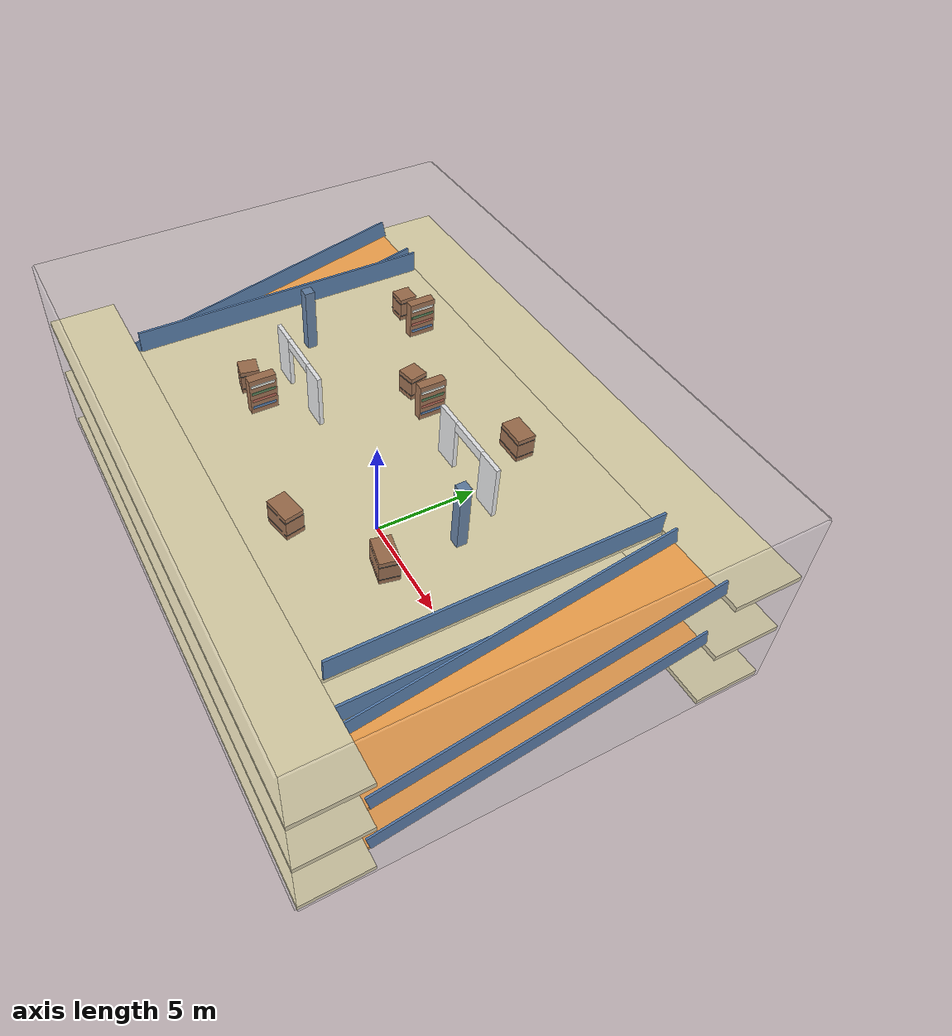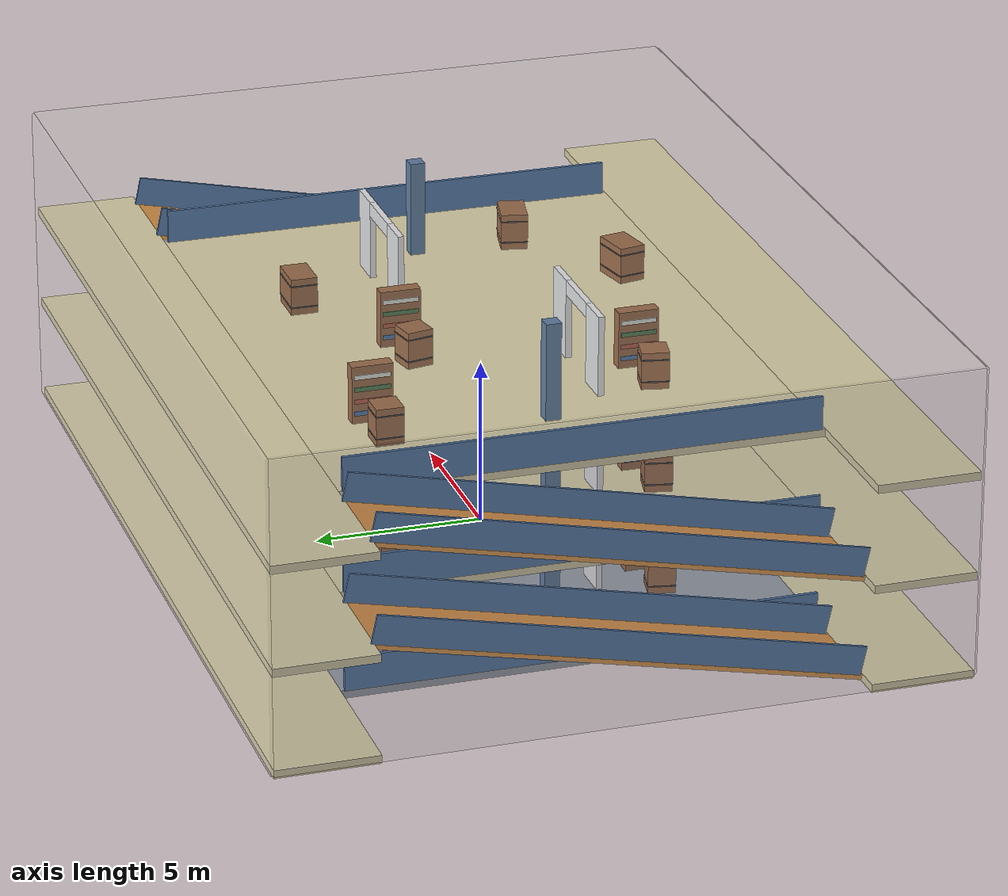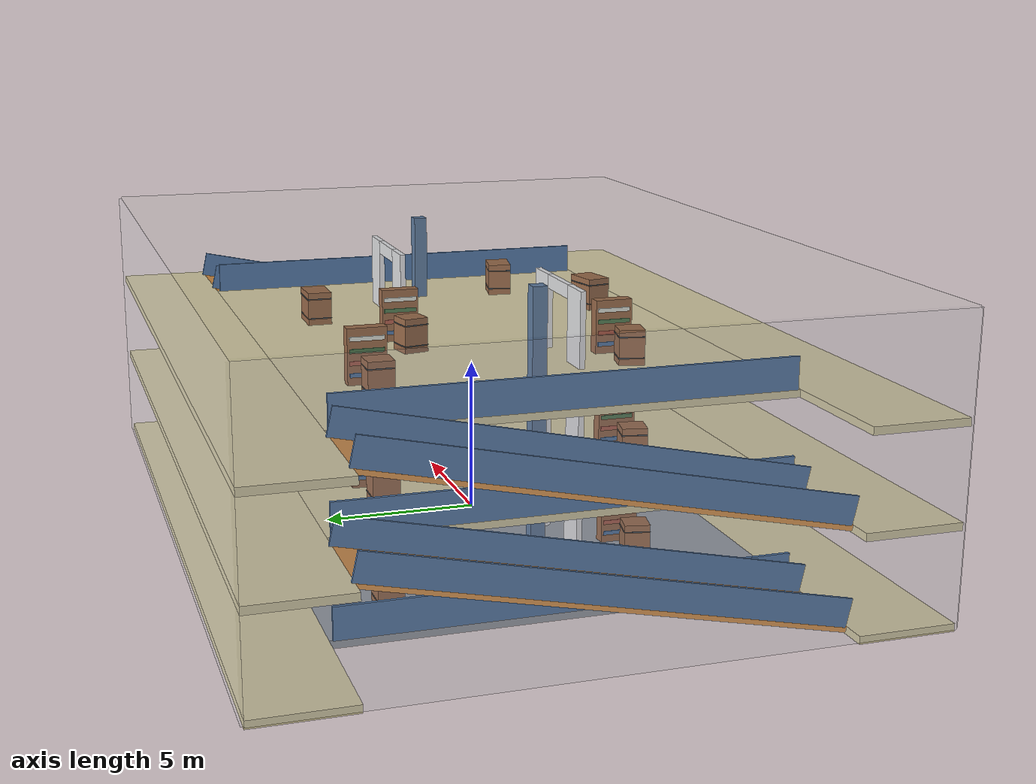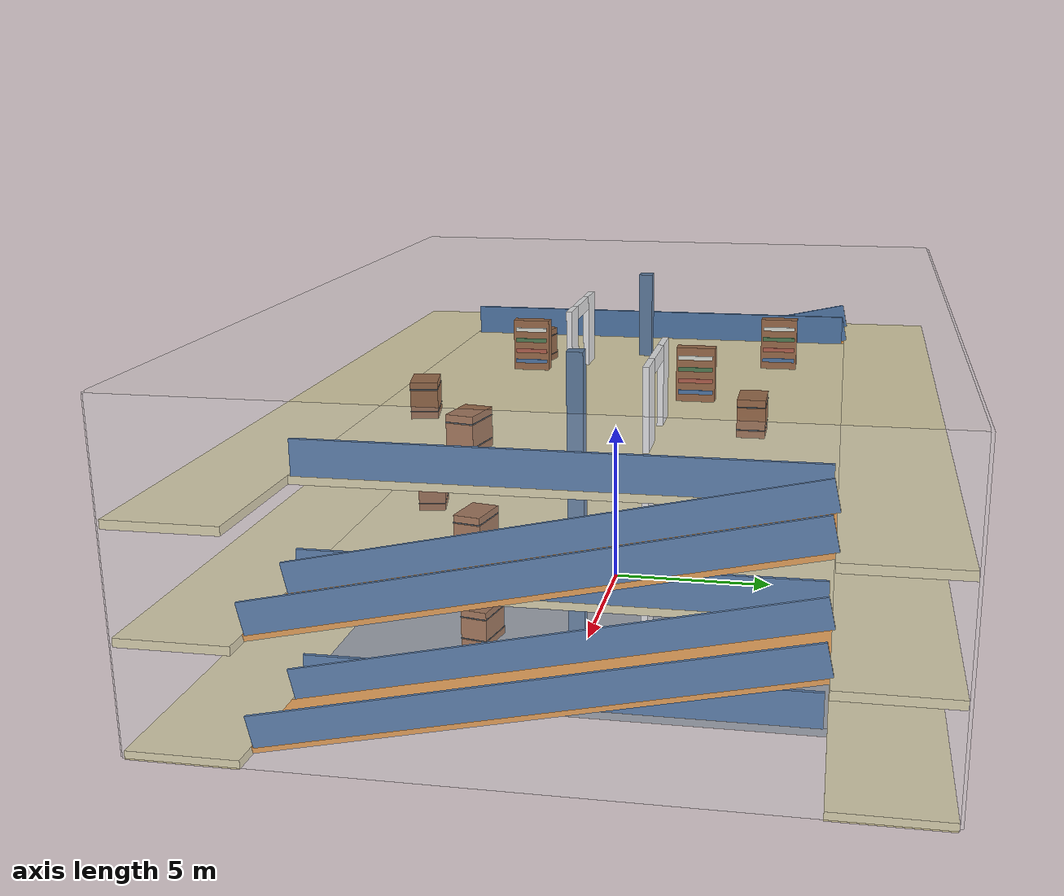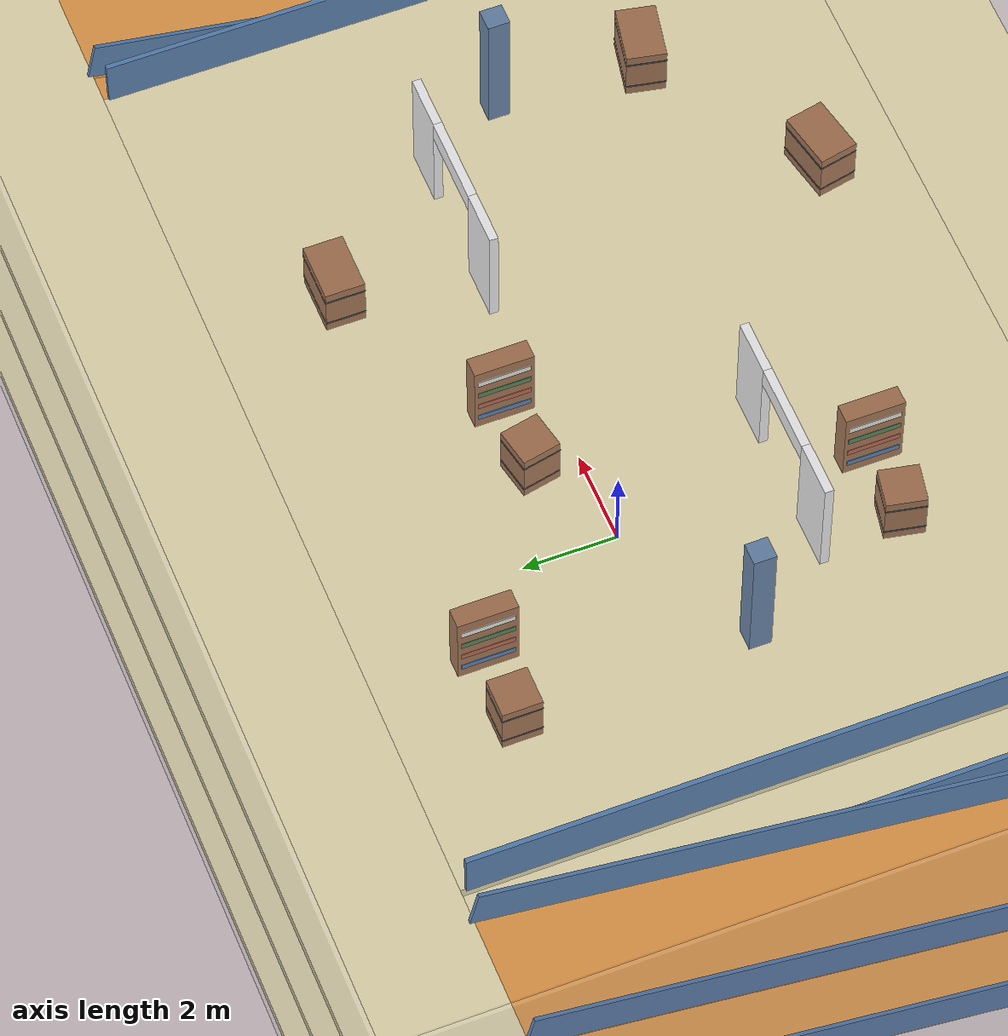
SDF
<?xml version='1.0' encoding='utf-8'?>
<sdf version="1.7">
  <world name="floor_M5">
    <gravity>0 0 -9.8</gravity>
    <plugin name="gazebo_ros_state" filename="libgazebo_ros_state.so">
      <ros>
        <namespace>/gazebo</namespace>
      </ros>
    </plugin>
    <physics name="ode_physics" type="ode">
      <max_step_size>0.001</max_step_size>
      <real_time_factor>1</real_time_factor>
      <real_time_update_rate>1000</real_time_update_rate>
      <ode>
        <solver>
          <type>quick</type>
          <iters>150</iters>
          <sor>1.3</sor>
        </solver>
        <constraints>
          <cfm>0</cfm>
          <erp>0.2</erp>
          <contact_max_correcting_vel>0.2</contact_max_correcting_vel>
          <contact_surface_layer>0.001</contact_surface_layer>
        </constraints>
      </ode>
    </physics>
    <light name="sun" type="directional">
      <pose>0 0 28 0 0 0</pose>
      <diffuse>0.92 0.91 0.88 1</diffuse>
      <specular>0.18 0.18 0.16 1</specular>
      <direction>-0.35 -0.28 -0.9</direction>
      <cast_shadows>true</cast_shadows>
    </light>
    <light name="fill" type="point">
      <pose>0 0 4.5 0 0 0</pose>
      <diffuse>0.45 0.48 0.52 1</diffuse>
      <specular>0.02 0.02 0.02 1</specular>
      <cast_shadows>false</cast_shadows>
      <attenuation>
        <range>80</range>
        <constant>0.5</constant>
        <linear>0.02</linear>
      </attenuation>
    </light>
    <scene>
      <ambient>0.48 0.49 0.53 1</ambient>
      <background>0.72 0.77 0.84 1</background>
    </scene>
    <gui fullscreen="false">
      <camera name="user_camera">
        <pose>18.9 -18 22.95 0 0.65 2.2</pose>
        <view_controller>orbit</view_controller>
      </camera>
    </gui>
    <model name="floor_M5_structure">
      <static>true</static>
      <link name="structure">
        <collision name="outer_south_wall_0_collision">
          <pose>0 -10 4.45 0 0 0</pose>
          <geometry>
            <box>
              <size>27 0.18 9.2</size>
            </box>
          </geometry>
          <max_contacts>40</max_contacts>
          <surface>
            <friction>
              <ode>
                <mu>2</mu>
                <mu2>2</mu2>
              </ode>
            </friction>
            <contact>
              <ode>
                <kp>1e7</kp>
                <kd>1000</kd>
                <max_vel>0.1</max_vel>
                <min_depth>0.001</min_depth>
              </ode>
            </contact>
          </surface>
        </collision>
        <visual name="outer_south_wall_0_visual">
          <pose>0 -10 4.45 0 0 0</pose>
          <geometry>
            <box>
              <size>27 0.18 9.2</size>
            </box>
          </geometry>
          <material>
            <ambient>0.91 0.91 0.93 1</ambient>
            <diffuse>0.91 0.91 0.93 1</diffuse>
          </material>
          <transparency>0.72</transparency>
        </visual>
        <collision name="outer_north_wall_0_collision">
          <pose>0 10 4.45 0 0 0</pose>
          <geometry>
            <box>
              <size>27 0.18 9.2</size>
            </box>
          </geometry>
          <max_contacts>40</max_contacts>
          <surface>
            <friction>
              <ode>
                <mu>2</mu>
                <mu2>2</mu2>
              </ode>
            </friction>
            <contact>
              <ode>
                <kp>1e7</kp>
                <kd>1000</kd>
                <max_vel>0.1</max_vel>
                <min_depth>0.001</min_depth>
              </ode>
            </contact>
          </surface>
        </collision>
        <visual name="outer_north_wall_0_visual">
          <pose>0 10 4.45 0 0 0</pose>
          <geometry>
            <box>
              <size>27 0.18 9.2</size>
            </box>
          </geometry>
          <material>
            <ambient>0.91 0.91 0.93 1</ambient>
            <diffuse>0.91 0.91 0.93 1</diffuse>
          </material>
          <transparency>0.72</transparency>
        </visual>
        <collision name="outer_west_wall_0_collision">
          <pose>-13.5 0 4.45 0 0 1.57079633</pose>
          <geometry>
            <box>
              <size>20 0.18 9.2</size>
            </box>
          </geometry>
          <max_contacts>40</max_contacts>
          <surface>
            <friction>
              <ode>
                <mu>2</mu>
                <mu2>2</mu2>
              </ode>
            </friction>
            <contact>
              <ode>
                <kp>1e7</kp>
                <kd>1000</kd>
                <max_vel>0.1</max_vel>
                <min_depth>0.001</min_depth>
              </ode>
            </contact>
          </surface>
        </collision>
        <visual name="outer_west_wall_0_visual">
          <pose>-13.5 0 4.45 0 0 1.57079633</pose>
          <geometry>
            <box>
              <size>20 0.18 9.2</size>
            </box>
          </geometry>
          <material>
            <ambient>0.91 0.91 0.93 1</ambient>
            <diffuse>0.91 0.91 0.93 1</diffuse>
          </material>
          <transparency>0.72</transparency>
        </visual>
        <collision name="outer_east_wall_0_collision">
          <pose>13.5 0 4.45 0 0 1.57079633</pose>
          <geometry>
            <box>
              <size>20 0.18 9.2</size>
            </box>
          </geometry>
          <max_contacts>40</max_contacts>
          <surface>
            <friction>
              <ode>
                <mu>2</mu>
                <mu2>2</mu2>
              </ode>
            </friction>
            <contact>
              <ode>
                <kp>1e7</kp>
                <kd>1000</kd>
                <max_vel>0.1</max_vel>
                <min_depth>0.001</min_depth>
              </ode>
            </contact>
          </surface>
        </collision>
        <visual name="outer_east_wall_0_visual">
          <pose>13.5 0 4.45 0 0 1.57079633</pose>
          <geometry>
            <box>
              <size>20 0.18 9.2</size>
            </box>
          </geometry>
          <material>
            <ambient>0.91 0.91 0.93 1</ambient>
            <diffuse>0.91 0.91 0.93 1</diffuse>
          </material>
          <transparency>0.72</transparency>
        </visual>
        <collision name="L1_floor_main_collision">
          <pose>0 0 -0.12 0 0 0</pose>
          <geometry>
            <box>
              <size>19 14 0.24</size>
            </box>
          </geometry>
          <max_contacts>40</max_contacts>
          <surface>
            <friction>
              <ode>
                <mu>2</mu>
                <mu2>2</mu2>
              </ode>
            </friction>
            <contact>
              <ode>
                <kp>1e7</kp>
                <kd>1000</kd>
                <max_vel>0.1</max_vel>
                <min_depth>0.001</min_depth>
              </ode>
            </contact>
          </surface>
        </collision>
        <visual name="L1_floor_main_visual">
          <pose>0 0 -0.12 0 0 0</pose>
          <geometry>
            <box>
              <size>19 14 0.24</size>
            </box>
          </geometry>
          <material>
            <ambient>0.54 0.57 0.62 1</ambient>
            <diffuse>0.54 0.57 0.62 1</diffuse>
          </material>
        </visual>
        <collision name="L1_floor_landing-1_collision">
          <pose>0 -8.5 -0.12 0 0 0</pose>
          <geometry>
            <box>
              <size>27 3 0.24</size>
            </box>
          </geometry>
          <max_contacts>40</max_contacts>
          <surface>
            <friction>
              <ode>
                <mu>2</mu>
                <mu2>2</mu2>
              </ode>
            </friction>
            <contact>
              <ode>
                <kp>1e7</kp>
                <kd>1000</kd>
                <max_vel>0.1</max_vel>
                <min_depth>0.001</min_depth>
              </ode>
            </contact>
          </surface>
        </collision>
        <visual name="L1_floor_landing-1_visual">
          <pose>0 -8.5 -0.12 0 0 0</pose>
          <geometry>
            <box>
              <size>27 3 0.24</size>
            </box>
          </geometry>
          <material>
            <ambient>0.86 0.81 0.62 1</ambient>
            <diffuse>0.86 0.81 0.62 1</diffuse>
          </material>
        </visual>
        <collision name="L1_floor_landing1_collision">
          <pose>0 8.5 -0.12 0 0 0</pose>
          <geometry>
            <box>
              <size>27 3 0.24</size>
            </box>
          </geometry>
          <max_contacts>40</max_contacts>
          <surface>
            <friction>
              <ode>
                <mu>2</mu>
                <mu2>2</mu2>
              </ode>
            </friction>
            <contact>
              <ode>
                <kp>1e7</kp>
                <kd>1000</kd>
                <max_vel>0.1</max_vel>
                <min_depth>0.001</min_depth>
              </ode>
            </contact>
          </surface>
        </collision>
        <visual name="L1_floor_landing1_visual">
          <pose>0 8.5 -0.12 0 0 0</pose>
          <geometry>
            <box>
              <size>27 3 0.24</size>
            </box>
          </geometry>
          <material>
            <ambient>0.86 0.81 0.62 1</ambient>
            <diffuse>0.86 0.81 0.62 1</diffuse>
          </material>
        </visual>
        <collision name="L1_shaft_rail-1_collision">
          <pose>-9.5 0 0.5 0 0 0</pose>
          <geometry>
            <box>
              <size>0.1 13.8 1</size>
            </box>
          </geometry>
          <max_contacts>40</max_contacts>
          <surface>
            <friction>
              <ode>
                <mu>2</mu>
                <mu2>2</mu2>
              </ode>
            </friction>
            <contact>
              <ode>
                <kp>1e7</kp>
                <kd>1000</kd>
                <max_vel>0.1</max_vel>
                <min_depth>0.001</min_depth>
              </ode>
            </contact>
          </surface>
        </collision>
        <visual name="L1_shaft_rail-1_visual">
          <pose>-9.5 0 0.5 0 0 0</pose>
          <geometry>
            <box>
              <size>0.1 13.8 1</size>
            </box>
          </geometry>
          <material>
            <ambient>0.19 0.38 0.62 1</ambient>
            <diffuse>0.19 0.38 0.62 1</diffuse>
          </material>
        </visual>
        <collision name="L1_shaft_rail1_collision">
          <pose>9.5 0 0.5 0 0 0</pose>
          <geometry>
            <box>
              <size>0.1 13.8 1</size>
            </box>
          </geometry>
          <max_contacts>40</max_contacts>
          <surface>
            <friction>
              <ode>
                <mu>2</mu>
                <mu2>2</mu2>
              </ode>
            </friction>
            <contact>
              <ode>
                <kp>1e7</kp>
                <kd>1000</kd>
                <max_vel>0.1</max_vel>
                <min_depth>0.001</min_depth>
              </ode>
            </contact>
          </surface>
        </collision>
        <visual name="L1_shaft_rail1_visual">
          <pose>9.5 0 0.5 0 0 0</pose>
          <geometry>
            <box>
              <size>0.1 13.8 1</size>
            </box>
          </geometry>
          <material>
            <ambient>0.19 0.38 0.62 1</ambient>
            <diffuse>0.19 0.38 0.62 1</diffuse>
          </material>
        </visual>
        <collision name="L1_column_prop-6.5_collision">
          <pose>-6.5 0 1.45 0 0 0</pose>
          <geometry>
            <box>
              <size>0.45 0.45 2.9</size>
            </box>
          </geometry>
          <max_contacts>40</max_contacts>
          <surface>
            <friction>
              <ode>
                <mu>2</mu>
                <mu2>2</mu2>
              </ode>
            </friction>
            <contact>
              <ode>
                <kp>1e7</kp>
                <kd>1000</kd>
                <max_vel>0.1</max_vel>
                <min_depth>0.001</min_depth>
              </ode>
            </contact>
          </surface>
        </collision>
        <visual name="L1_column_prop-6.5_visual">
          <pose>-6.5 0 1.45 0 0 0</pose>
          <geometry>
            <box>
              <size>0.45 0.45 2.9</size>
            </box>
          </geometry>
          <material>
            <ambient>0.26 0.40 0.58 1</ambient>
            <diffuse>0.26 0.40 0.58 1</diffuse>
          </material>
        </visual>
        <collision name="L1_column_prop6.5_collision">
          <pose>6.5 0 1.45 0 0 0</pose>
          <geometry>
            <box>
              <size>0.45 0.45 2.9</size>
            </box>
          </geometry>
          <max_contacts>40</max_contacts>
          <surface>
            <friction>
              <ode>
                <mu>2</mu>
                <mu2>2</mu2>
              </ode>
            </friction>
            <contact>
              <ode>
                <kp>1e7</kp>
                <kd>1000</kd>
                <max_vel>0.1</max_vel>
                <min_depth>0.001</min_depth>
              </ode>
            </contact>
          </surface>
        </collision>
        <visual name="L1_column_prop6.5_visual">
          <pose>6.5 0 1.45 0 0 0</pose>
          <geometry>
            <box>
              <size>0.45 0.45 2.9</size>
            </box>
          </geometry>
          <material>
            <ambient>0.26 0.40 0.58 1</ambient>
            <diffuse>0.26 0.40 0.58 1</diffuse>
          </material>
        </visual>
        <collision name="L1_store0_prop_collision">
          <pose>-5.9 -3.5 0.55 0 0 -0.2</pose>
          <geometry>
            <box>
              <size>0.8 0.8 1.1</size>
            </box>
          </geometry>
          <max_contacts>40</max_contacts>
          <surface>
            <friction>
              <ode>
                <mu>2</mu>
                <mu2>2</mu2>
              </ode>
            </friction>
            <contact>
              <ode>
                <kp>1e7</kp>
                <kd>1000</kd>
                <max_vel>0.1</max_vel>
                <min_depth>0.001</min_depth>
              </ode>
            </contact>
          </surface>
        </collision>
        <visual name="L1_store0_prop_visual">
          <pose>-5.9 -3.5 0.55 0 0 -0.2</pose>
          <geometry>
            <box>
              <size>0.8 0.8 1.1</size>
            </box>
          </geometry>
          <material>
            <ambient>0.55 0.32 0.17 1</ambient>
            <diffuse>0.55 0.32 0.17 1</diffuse>
          </material>
        </visual>
        <visual name="L1_store0_strap_-1_visual">
          <pose>-5.9 -3.5 0.22 0 0 -0.2</pose>
          <geometry>
            <box>
              <size>0.812 0.812 0.035</size>
            </box>
          </geometry>
          <material>
            <ambient>0.15 0.18 0.21 1</ambient>
            <diffuse>0.15 0.18 0.21 1</diffuse>
          </material>
        </visual>
        <visual name="L1_store0_strap_1_visual">
          <pose>-5.9 -3.5 0.88 0 0 -0.2</pose>
          <geometry>
            <box>
              <size>0.812 0.812 0.035</size>
            </box>
          </geometry>
          <material>
            <ambient>0.15 0.18 0.21 1</ambient>
            <diffuse>0.15 0.18 0.21 1</diffuse>
          </material>
        </visual>
        <collision name="L1_shelf0_cabinet_prop_collision">
          <pose>-4.4 -3.5 0.85 0 0 1.57079633</pose>
          <geometry>
            <box>
              <size>1.2 0.4 1.7</size>
            </box>
          </geometry>
          <max_contacts>40</max_contacts>
          <surface>
            <friction>
              <ode>
                <mu>2</mu>
                <mu2>2</mu2>
              </ode>
            </friction>
            <contact>
              <ode>
                <kp>1e7</kp>
                <kd>1000</kd>
                <max_vel>0.1</max_vel>
                <min_depth>0.001</min_depth>
              </ode>
            </contact>
          </surface>
        </collision>
        <visual name="L1_shelf0_cabinet_prop_visual">
          <pose>-4.4 -3.5 0.85 0 0 1.57079633</pose>
          <geometry>
            <box>
              <size>1.2 0.4 1.7</size>
            </box>
          </geometry>
          <material>
            <ambient>0.55 0.32 0.17 1</ambient>
            <diffuse>0.55 0.32 0.17 1</diffuse>
          </material>
        </visual>
        <visual name="L1_shelf0_books_0_visual">
          <pose>-4.4 -3.5 0.3 0 0 1.57079633</pose>
          <geometry>
            <box>
              <size>1.06 0.43 0.13</size>
            </box>
          </geometry>
          <material>
            <ambient>0.19 0.38 0.62 1</ambient>
            <diffuse>0.19 0.38 0.62 1</diffuse>
          </material>
        </visual>
        <visual name="L1_shelf0_books_1_visual">
          <pose>-4.4 -3.5 0.66 0 0 1.57079633</pose>
          <geometry>
            <box>
              <size>1.06 0.43 0.13</size>
            </box>
          </geometry>
          <material>
            <ambient>0.67 0.26 0.18 1</ambient>
            <diffuse>0.67 0.26 0.18 1</diffuse>
          </material>
        </visual>
        <visual name="L1_shelf0_books_2_visual">
          <pose>-4.4 -3.5 1.02 0 0 1.57079633</pose>
          <geometry>
            <box>
              <size>1.06 0.43 0.13</size>
            </box>
          </geometry>
          <material>
            <ambient>0.19 0.40 0.20 1</ambient>
            <diffuse>0.19 0.40 0.20 1</diffuse>
          </material>
        </visual>
        <visual name="L1_shelf0_books_3_visual">
          <pose>-4.4 -3.5 1.38 0 0 1.57079633</pose>
          <geometry>
            <box>
              <size>1.06 0.43 0.13</size>
            </box>
          </geometry>
          <material>
            <ambient>0.87 0.88 0.85 1</ambient>
            <diffuse>0.87 0.88 0.85 1</diffuse>
          </material>
        </visual>
        <collision name="L1_store1_prop_collision">
          <pose>2.6 4.5 0.55 0 0 0</pose>
          <geometry>
            <box>
              <size>1.2 0.8 1.1</size>
            </box>
          </geometry>
          <max_contacts>40</max_contacts>
          <surface>
            <friction>
              <ode>
                <mu>2</mu>
                <mu2>2</mu2>
              </ode>
            </friction>
            <contact>
              <ode>
                <kp>1e7</kp>
                <kd>1000</kd>
                <max_vel>0.1</max_vel>
                <min_depth>0.001</min_depth>
              </ode>
            </contact>
          </surface>
        </collision>
        <visual name="L1_store1_prop_visual">
          <pose>2.6 4.5 0.55 0 0 0</pose>
          <geometry>
            <box>
              <size>1.2 0.8 1.1</size>
            </box>
          </geometry>
          <material>
            <ambient>0.55 0.32 0.17 1</ambient>
            <diffuse>0.55 0.32 0.17 1</diffuse>
          </material>
        </visual>
        <visual name="L1_store1_strap_-1_visual">
          <pose>2.6 4.5 0.22 0 0 0</pose>
          <geometry>
            <box>
              <size>1.212 0.812 0.035</size>
            </box>
          </geometry>
          <material>
            <ambient>0.15 0.18 0.21 1</ambient>
            <diffuse>0.15 0.18 0.21 1</diffuse>
          </material>
        </visual>
        <visual name="L1_store1_strap_1_visual">
          <pose>2.6 4.5 0.88 0 0 0</pose>
          <geometry>
            <box>
              <size>1.212 0.812 0.035</size>
            </box>
          </geometry>
          <material>
            <ambient>0.15 0.18 0.21 1</ambient>
            <diffuse>0.15 0.18 0.21 1</diffuse>
          </material>
        </visual>
        <collision name="L1_store2_prop_collision">
          <pose>-2.4 2.5 0.55 0 0 0.2</pose>
          <geometry>
            <box>
              <size>0.8 0.8 1.1</size>
            </box>
          </geometry>
          <max_contacts>40</max_contacts>
          <surface>
            <friction>
              <ode>
                <mu>2</mu>
                <mu2>2</mu2>
              </ode>
            </friction>
            <contact>
              <ode>
                <kp>1e7</kp>
                <kd>1000</kd>
                <max_vel>0.1</max_vel>
                <min_depth>0.001</min_depth>
              </ode>
            </contact>
          </surface>
        </collision>
        <visual name="L1_store2_prop_visual">
          <pose>-2.4 2.5 0.55 0 0 0.2</pose>
          <geometry>
            <box>
              <size>0.8 0.8 1.1</size>
            </box>
          </geometry>
          <material>
            <ambient>0.55 0.32 0.17 1</ambient>
            <diffuse>0.55 0.32 0.17 1</diffuse>
          </material>
        </visual>
        <visual name="L1_store2_strap_-1_visual">
          <pose>-2.4 2.5 0.22 0 0 0.2</pose>
          <geometry>
            <box>
              <size>0.812 0.812 0.035</size>
            </box>
          </geometry>
          <material>
            <ambient>0.15 0.18 0.21 1</ambient>
            <diffuse>0.15 0.18 0.21 1</diffuse>
          </material>
        </visual>
        <visual name="L1_store2_strap_1_visual">
          <pose>-2.4 2.5 0.88 0 0 0.2</pose>
          <geometry>
            <box>
              <size>0.812 0.812 0.035</size>
            </box>
          </geometry>
          <material>
            <ambient>0.15 0.18 0.21 1</ambient>
            <diffuse>0.15 0.18 0.21 1</diffuse>
          </material>
        </visual>
        <collision name="L1_shelf2_cabinet_prop_collision">
          <pose>-0.9 2.5 0.85 0 0 1.57079633</pose>
          <geometry>
            <box>
              <size>1.2 0.4 1.7</size>
            </box>
          </geometry>
          <max_contacts>40</max_contacts>
          <surface>
            <friction>
              <ode>
                <mu>2</mu>
                <mu2>2</mu2>
              </ode>
            </friction>
            <contact>
              <ode>
                <kp>1e7</kp>
                <kd>1000</kd>
                <max_vel>0.1</max_vel>
                <min_depth>0.001</min_depth>
              </ode>
            </contact>
          </surface>
        </collision>
        <visual name="L1_shelf2_cabinet_prop_visual">
          <pose>-0.9 2.5 0.85 0 0 1.57079633</pose>
          <geometry>
            <box>
              <size>1.2 0.4 1.7</size>
            </box>
          </geometry>
          <material>
            <ambient>0.55 0.32 0.17 1</ambient>
            <diffuse>0.55 0.32 0.17 1</diffuse>
          </material>
        </visual>
        <visual name="L1_shelf2_books_0_visual">
          <pose>-0.9 2.5 0.3 0 0 1.57079633</pose>
          <geometry>
            <box>
              <size>1.06 0.43 0.13</size>
            </box>
          </geometry>
          <material>
            <ambient>0.19 0.38 0.62 1</ambient>
            <diffuse>0.19 0.38 0.62 1</diffuse>
          </material>
        </visual>
        <visual name="L1_shelf2_books_1_visual">
          <pose>-0.9 2.5 0.66 0 0 1.57079633</pose>
          <geometry>
            <box>
              <size>1.06 0.43 0.13</size>
            </box>
          </geometry>
          <material>
            <ambient>0.67 0.26 0.18 1</ambient>
            <diffuse>0.67 0.26 0.18 1</diffuse>
          </material>
        </visual>
        <visual name="L1_shelf2_books_2_visual">
          <pose>-0.9 2.5 1.02 0 0 1.57079633</pose>
          <geometry>
            <box>
              <size>1.06 0.43 0.13</size>
            </box>
          </geometry>
          <material>
            <ambient>0.19 0.40 0.20 1</ambient>
            <diffuse>0.19 0.40 0.20 1</diffuse>
          </material>
        </visual>
        <visual name="L1_shelf2_books_3_visual">
          <pose>-0.9 2.5 1.38 0 0 1.57079633</pose>
          <geometry>
            <box>
              <size>1.06 0.43 0.13</size>
            </box>
          </geometry>
          <material>
            <ambient>0.87 0.88 0.85 1</ambient>
            <diffuse>0.87 0.88 0.85 1</diffuse>
          </material>
        </visual>
        <collision name="L1_store3_prop_collision">
          <pose>5.6 -3 0.55 0 0 -0.2</pose>
          <geometry>
            <box>
              <size>1.2 0.8 1.1</size>
            </box>
          </geometry>
          <max_contacts>40</max_contacts>
          <surface>
            <friction>
              <ode>
                <mu>2</mu>
                <mu2>2</mu2>
              </ode>
            </friction>
            <contact>
              <ode>
                <kp>1e7</kp>
                <kd>1000</kd>
                <max_vel>0.1</max_vel>
                <min_depth>0.001</min_depth>
              </ode>
            </contact>
          </surface>
        </collision>
        <visual name="L1_store3_prop_visual">
          <pose>5.6 -3 0.55 0 0 -0.2</pose>
          <geometry>
            <box>
              <size>1.2 0.8 1.1</size>
            </box>
          </geometry>
          <material>
            <ambient>0.55 0.32 0.17 1</ambient>
            <diffuse>0.55 0.32 0.17 1</diffuse>
          </material>
        </visual>
        <visual name="L1_store3_strap_-1_visual">
          <pose>5.6 -3 0.22 0 0 -0.2</pose>
          <geometry>
            <box>
              <size>1.212 0.812 0.035</size>
            </box>
          </geometry>
          <material>
            <ambient>0.15 0.18 0.21 1</ambient>
            <diffuse>0.15 0.18 0.21 1</diffuse>
          </material>
        </visual>
        <visual name="L1_store3_strap_1_visual">
          <pose>5.6 -3 0.88 0 0 -0.2</pose>
          <geometry>
            <box>
              <size>1.212 0.812 0.035</size>
            </box>
          </geometry>
          <material>
            <ambient>0.15 0.18 0.21 1</ambient>
            <diffuse>0.15 0.18 0.21 1</diffuse>
          </material>
        </visual>
        <collision name="L1_store4_prop_collision">
          <pose>-7.4 4.8 0.55 0 0 0</pose>
          <geometry>
            <box>
              <size>0.8 0.8 1.1</size>
            </box>
          </geometry>
          <max_contacts>40</max_contacts>
          <surface>
            <friction>
              <ode>
                <mu>2</mu>
                <mu2>2</mu2>
              </ode>
            </friction>
            <contact>
              <ode>
                <kp>1e7</kp>
                <kd>1000</kd>
                <max_vel>0.1</max_vel>
                <min_depth>0.001</min_depth>
              </ode>
            </contact>
          </surface>
        </collision>
        <visual name="L1_store4_prop_visual">
          <pose>-7.4 4.8 0.55 0 0 0</pose>
          <geometry>
            <box>
              <size>0.8 0.8 1.1</size>
            </box>
          </geometry>
          <material>
            <ambient>0.55 0.32 0.17 1</ambient>
            <diffuse>0.55 0.32 0.17 1</diffuse>
          </material>
        </visual>
        <visual name="L1_store4_strap_-1_visual">
          <pose>-7.4 4.8 0.22 0 0 0</pose>
          <geometry>
            <box>
              <size>0.812 0.812 0.035</size>
            </box>
          </geometry>
          <material>
            <ambient>0.15 0.18 0.21 1</ambient>
            <diffuse>0.15 0.18 0.21 1</diffuse>
          </material>
        </visual>
        <visual name="L1_store4_strap_1_visual">
          <pose>-7.4 4.8 0.88 0 0 0</pose>
          <geometry>
            <box>
              <size>0.812 0.812 0.035</size>
            </box>
          </geometry>
          <material>
            <ambient>0.15 0.18 0.21 1</ambient>
            <diffuse>0.15 0.18 0.21 1</diffuse>
          </material>
        </visual>
        <collision name="L1_shelf4_cabinet_prop_collision">
          <pose>-5.9 4.8 0.85 0 0 1.57079633</pose>
          <geometry>
            <box>
              <size>1.2 0.4 1.7</size>
            </box>
          </geometry>
          <max_contacts>40</max_contacts>
          <surface>
            <friction>
              <ode>
                <mu>2</mu>
                <mu2>2</mu2>
              </ode>
            </friction>
            <contact>
              <ode>
                <kp>1e7</kp>
                <kd>1000</kd>
                <max_vel>0.1</max_vel>
                <min_depth>0.001</min_depth>
              </ode>
            </contact>
          </surface>
        </collision>
        <visual name="L1_shelf4_cabinet_prop_visual">
          <pose>-5.9 4.8 0.85 0 0 1.57079633</pose>
          <geometry>
            <box>
              <size>1.2 0.4 1.7</size>
            </box>
          </geometry>
          <material>
            <ambient>0.55 0.32 0.17 1</ambient>
            <diffuse>0.55 0.32 0.17 1</diffuse>
          </material>
        </visual>
        <visual name="L1_shelf4_books_0_visual">
          <pose>-5.9 4.8 0.3 0 0 1.57079633</pose>
          <geometry>
            <box>
              <size>1.06 0.43 0.13</size>
            </box>
          </geometry>
          <material>
            <ambient>0.19 0.38 0.62 1</ambient>
            <diffuse>0.19 0.38 0.62 1</diffuse>
          </material>
        </visual>
        <visual name="L1_shelf4_books_1_visual">
          <pose>-5.9 4.8 0.66 0 0 1.57079633</pose>
          <geometry>
            <box>
              <size>1.06 0.43 0.13</size>
            </box>
          </geometry>
          <material>
            <ambient>0.67 0.26 0.18 1</ambient>
            <diffuse>0.67 0.26 0.18 1</diffuse>
          </material>
        </visual>
        <visual name="L1_shelf4_books_2_visual">
          <pose>-5.9 4.8 1.02 0 0 1.57079633</pose>
          <geometry>
            <box>
              <size>1.06 0.43 0.13</size>
            </box>
          </geometry>
          <material>
            <ambient>0.19 0.40 0.20 1</ambient>
            <diffuse>0.19 0.40 0.20 1</diffuse>
          </material>
        </visual>
        <visual name="L1_shelf4_books_3_visual">
          <pose>-5.9 4.8 1.38 0 0 1.57079633</pose>
          <geometry>
            <box>
              <size>1.06 0.43 0.13</size>
            </box>
          </geometry>
          <material>
            <ambient>0.87 0.88 0.85 1</ambient>
            <diffuse>0.87 0.88 0.85 1</diffuse>
          </material>
        </visual>
        <collision name="L1_store5_prop_collision">
          <pose>2.1 -5.3 0.55 0 0 0.2</pose>
          <geometry>
            <box>
              <size>1.2 0.8 1.1</size>
            </box>
          </geometry>
          <max_contacts>40</max_contacts>
          <surface>
            <friction>
              <ode>
                <mu>2</mu>
                <mu2>2</mu2>
              </ode>
            </friction>
            <contact>
              <ode>
                <kp>1e7</kp>
                <kd>1000</kd>
                <max_vel>0.1</max_vel>
                <min_depth>0.001</min_depth>
              </ode>
            </contact>
          </surface>
        </collision>
        <visual name="L1_store5_prop_visual">
          <pose>2.1 -5.3 0.55 0 0 0.2</pose>
          <geometry>
            <box>
              <size>1.2 0.8 1.1</size>
            </box>
          </geometry>
          <material>
            <ambient>0.55 0.32 0.17 1</ambient>
            <diffuse>0.55 0.32 0.17 1</diffuse>
          </material>
        </visual>
        <visual name="L1_store5_strap_-1_visual">
          <pose>2.1 -5.3 0.22 0 0 0.2</pose>
          <geometry>
            <box>
              <size>1.212 0.812 0.035</size>
            </box>
          </geometry>
          <material>
            <ambient>0.15 0.18 0.21 1</ambient>
            <diffuse>0.15 0.18 0.21 1</diffuse>
          </material>
        </visual>
        <visual name="L1_store5_strap_1_visual">
          <pose>2.1 -5.3 0.88 0 0 0.2</pose>
          <geometry>
            <box>
              <size>1.212 0.812 0.035</size>
            </box>
          </geometry>
          <material>
            <ambient>0.15 0.18 0.21 1</ambient>
            <diffuse>0.15 0.18 0.21 1</diffuse>
          </material>
        </visual>
        <collision name="L1_partition0_wall_0_collision">
          <pose>-4.95 -1.8 1.15 0 0 0</pose>
          <geometry>
            <box>
              <size>1.1 0.18 2.5</size>
            </box>
          </geometry>
          <max_contacts>40</max_contacts>
          <surface>
            <friction>
              <ode>
                <mu>2</mu>
                <mu2>2</mu2>
              </ode>
            </friction>
            <contact>
              <ode>
                <kp>1e7</kp>
                <kd>1000</kd>
                <max_vel>0.1</max_vel>
                <min_depth>0.001</min_depth>
              </ode>
            </contact>
          </surface>
        </collision>
        <visual name="L1_partition0_wall_0_visual">
          <pose>-4.95 -1.8 1.15 0 0 0</pose>
          <geometry>
            <box>
              <size>1.1 0.18 2.5</size>
            </box>
          </geometry>
          <material>
            <ambient>0.91 0.91 0.93 1</ambient>
            <diffuse>0.91 0.91 0.93 1</diffuse>
          </material>
        </visual>
        <collision name="L1_partition0_wall_1_collision">
          <pose>-2.05 -1.8 1.15 0 0 0</pose>
          <geometry>
            <box>
              <size>1.1 0.18 2.5</size>
            </box>
          </geometry>
          <max_contacts>40</max_contacts>
          <surface>
            <friction>
              <ode>
                <mu>2</mu>
                <mu2>2</mu2>
              </ode>
            </friction>
            <contact>
              <ode>
                <kp>1e7</kp>
                <kd>1000</kd>
                <max_vel>0.1</max_vel>
                <min_depth>0.001</min_depth>
              </ode>
            </contact>
          </surface>
        </collision>
        <visual name="L1_partition0_wall_1_visual">
          <pose>-2.05 -1.8 1.15 0 0 0</pose>
          <geometry>
            <box>
              <size>1.1 0.18 2.5</size>
            </box>
          </geometry>
          <material>
            <ambient>0.91 0.91 0.93 1</ambient>
            <diffuse>0.91 0.91 0.93 1</diffuse>
          </material>
        </visual>
        <collision name="L1_partition0_lintel_wall_collision">
          <pose>-3.5 -1.8 2.18 0 0 0</pose>
          <geometry>
            <box>
              <size>1.8 0.18 0.44</size>
            </box>
          </geometry>
          <max_contacts>40</max_contacts>
          <surface>
            <friction>
              <ode>
                <mu>2</mu>
                <mu2>2</mu2>
              </ode>
            </friction>
            <contact>
              <ode>
                <kp>1e7</kp>
                <kd>1000</kd>
                <max_vel>0.1</max_vel>
                <min_depth>0.001</min_depth>
              </ode>
            </contact>
          </surface>
        </collision>
        <visual name="L1_partition0_lintel_wall_visual">
          <pose>-3.5 -1.8 2.18 0 0 0</pose>
          <geometry>
            <box>
              <size>1.8 0.18 0.44</size>
            </box>
          </geometry>
          <material>
            <ambient>0.91 0.91 0.93 1</ambient>
            <diffuse>0.91 0.91 0.93 1</diffuse>
          </material>
        </visual>
        <collision name="L1_partition1_wall_0_collision">
          <pose>2.55 1.8 1.15 0 0 0</pose>
          <geometry>
            <box>
              <size>1.1 0.18 2.5</size>
            </box>
          </geometry>
          <max_contacts>40</max_contacts>
          <surface>
            <friction>
              <ode>
                <mu>2</mu>
                <mu2>2</mu2>
              </ode>
            </friction>
            <contact>
              <ode>
                <kp>1e7</kp>
                <kd>1000</kd>
                <max_vel>0.1</max_vel>
                <min_depth>0.001</min_depth>
              </ode>
            </contact>
          </surface>
        </collision>
        <visual name="L1_partition1_wall_0_visual">
          <pose>2.55 1.8 1.15 0 0 0</pose>
          <geometry>
            <box>
              <size>1.1 0.18 2.5</size>
            </box>
          </geometry>
          <material>
            <ambient>0.91 0.91 0.93 1</ambient>
            <diffuse>0.91 0.91 0.93 1</diffuse>
          </material>
        </visual>
        <collision name="L1_partition1_wall_1_collision">
          <pose>5.45 1.8 1.15 0 0 0</pose>
          <geometry>
            <box>
              <size>1.1 0.18 2.5</size>
            </box>
          </geometry>
          <max_contacts>40</max_contacts>
          <surface>
            <friction>
              <ode>
                <mu>2</mu>
                <mu2>2</mu2>
              </ode>
            </friction>
            <contact>
              <ode>
                <kp>1e7</kp>
                <kd>1000</kd>
                <max_vel>0.1</max_vel>
                <min_depth>0.001</min_depth>
              </ode>
            </contact>
          </surface>
        </collision>
        <visual name="L1_partition1_wall_1_visual">
          <pose>5.45 1.8 1.15 0 0 0</pose>
          <geometry>
            <box>
              <size>1.1 0.18 2.5</size>
            </box>
          </geometry>
          <material>
            <ambient>0.91 0.91 0.93 1</ambient>
            <diffuse>0.91 0.91 0.93 1</diffuse>
          </material>
        </visual>
        <collision name="L1_partition1_lintel_wall_collision">
          <pose>4 1.8 2.18 0 0 0</pose>
          <geometry>
            <box>
              <size>1.8 0.18 0.44</size>
            </box>
          </geometry>
          <max_contacts>40</max_contacts>
          <surface>
            <friction>
              <ode>
                <mu>2</mu>
                <mu2>2</mu2>
              </ode>
            </friction>
            <contact>
              <ode>
                <kp>1e7</kp>
                <kd>1000</kd>
                <max_vel>0.1</max_vel>
                <min_depth>0.001</min_depth>
              </ode>
            </contact>
          </surface>
        </collision>
        <visual name="L1_partition1_lintel_wall_visual">
          <pose>4 1.8 2.18 0 0 0</pose>
          <geometry>
            <box>
              <size>1.8 0.18 0.44</size>
            </box>
          </geometry>
          <material>
            <ambient>0.91 0.91 0.93 1</ambient>
            <diffuse>0.91 0.91 0.93 1</diffuse>
          </material>
        </visual>
        <collision name="L2_floor_main_collision">
          <pose>0 0 2.88 0 0 0</pose>
          <geometry>
            <box>
              <size>19 14 0.24</size>
            </box>
          </geometry>
          <max_contacts>40</max_contacts>
          <surface>
            <friction>
              <ode>
                <mu>2</mu>
                <mu2>2</mu2>
              </ode>
            </friction>
            <contact>
              <ode>
                <kp>1e7</kp>
                <kd>1000</kd>
                <max_vel>0.1</max_vel>
                <min_depth>0.001</min_depth>
              </ode>
            </contact>
          </surface>
        </collision>
        <visual name="L2_floor_main_visual">
          <pose>0 0 2.88 0 0 0</pose>
          <geometry>
            <box>
              <size>19 14 0.24</size>
            </box>
          </geometry>
          <material>
            <ambient>0.86 0.81 0.62 1</ambient>
            <diffuse>0.86 0.81 0.62 1</diffuse>
          </material>
        </visual>
        <collision name="L2_floor_landing-1_collision">
          <pose>0 -8.5 2.88 0 0 0</pose>
          <geometry>
            <box>
              <size>27 3 0.24</size>
            </box>
          </geometry>
          <max_contacts>40</max_contacts>
          <surface>
            <friction>
              <ode>
                <mu>2</mu>
                <mu2>2</mu2>
              </ode>
            </friction>
            <contact>
              <ode>
                <kp>1e7</kp>
                <kd>1000</kd>
                <max_vel>0.1</max_vel>
                <min_depth>0.001</min_depth>
              </ode>
            </contact>
          </surface>
        </collision>
        <visual name="L2_floor_landing-1_visual">
          <pose>0 -8.5 2.88 0 0 0</pose>
          <geometry>
            <box>
              <size>27 3 0.24</size>
            </box>
          </geometry>
          <material>
            <ambient>0.86 0.81 0.62 1</ambient>
            <diffuse>0.86 0.81 0.62 1</diffuse>
          </material>
        </visual>
        <collision name="L2_floor_landing1_collision">
          <pose>0 8.5 2.88 0 0 0</pose>
          <geometry>
            <box>
              <size>27 3 0.24</size>
            </box>
          </geometry>
          <max_contacts>40</max_contacts>
          <surface>
            <friction>
              <ode>
                <mu>2</mu>
                <mu2>2</mu2>
              </ode>
            </friction>
            <contact>
              <ode>
                <kp>1e7</kp>
                <kd>1000</kd>
                <max_vel>0.1</max_vel>
                <min_depth>0.001</min_depth>
              </ode>
            </contact>
          </surface>
        </collision>
        <visual name="L2_floor_landing1_visual">
          <pose>0 8.5 2.88 0 0 0</pose>
          <geometry>
            <box>
              <size>27 3 0.24</size>
            </box>
          </geometry>
          <material>
            <ambient>0.86 0.81 0.62 1</ambient>
            <diffuse>0.86 0.81 0.62 1</diffuse>
          </material>
        </visual>
        <collision name="L2_shaft_rail-1_collision">
          <pose>-9.5 0 3.5 0 0 0</pose>
          <geometry>
            <box>
              <size>0.1 13.8 1</size>
            </box>
          </geometry>
          <max_contacts>40</max_contacts>
          <surface>
            <friction>
              <ode>
                <mu>2</mu>
                <mu2>2</mu2>
              </ode>
            </friction>
            <contact>
              <ode>
                <kp>1e7</kp>
                <kd>1000</kd>
                <max_vel>0.1</max_vel>
                <min_depth>0.001</min_depth>
              </ode>
            </contact>
          </surface>
        </collision>
        <visual name="L2_shaft_rail-1_visual">
          <pose>-9.5 0 3.5 0 0 0</pose>
          <geometry>
            <box>
              <size>0.1 13.8 1</size>
            </box>
          </geometry>
          <material>
            <ambient>0.19 0.38 0.62 1</ambient>
            <diffuse>0.19 0.38 0.62 1</diffuse>
          </material>
        </visual>
        <collision name="L2_shaft_rail1_collision">
          <pose>9.5 0 3.5 0 0 0</pose>
          <geometry>
            <box>
              <size>0.1 13.8 1</size>
            </box>
          </geometry>
          <max_contacts>40</max_contacts>
          <surface>
            <friction>
              <ode>
                <mu>2</mu>
                <mu2>2</mu2>
              </ode>
            </friction>
            <contact>
              <ode>
                <kp>1e7</kp>
                <kd>1000</kd>
                <max_vel>0.1</max_vel>
                <min_depth>0.001</min_depth>
              </ode>
            </contact>
          </surface>
        </collision>
        <visual name="L2_shaft_rail1_visual">
          <pose>9.5 0 3.5 0 0 0</pose>
          <geometry>
            <box>
              <size>0.1 13.8 1</size>
            </box>
          </geometry>
          <material>
            <ambient>0.19 0.38 0.62 1</ambient>
            <diffuse>0.19 0.38 0.62 1</diffuse>
          </material>
        </visual>
        <collision name="L2_column_prop-6.5_collision">
          <pose>-6.5 0 4.45 0 0 0</pose>
          <geometry>
            <box>
              <size>0.45 0.45 2.9</size>
            </box>
          </geometry>
          <max_contacts>40</max_contacts>
          <surface>
            <friction>
              <ode>
                <mu>2</mu>
                <mu2>2</mu2>
              </ode>
            </friction>
            <contact>
              <ode>
                <kp>1e7</kp>
                <kd>1000</kd>
                <max_vel>0.1</max_vel>
                <min_depth>0.001</min_depth>
              </ode>
            </contact>
          </surface>
        </collision>
        <visual name="L2_column_prop-6.5_visual">
          <pose>-6.5 0 4.45 0 0 0</pose>
          <geometry>
            <box>
              <size>0.45 0.45 2.9</size>
            </box>
          </geometry>
          <material>
            <ambient>0.26 0.40 0.58 1</ambient>
            <diffuse>0.26 0.40 0.58 1</diffuse>
          </material>
        </visual>
        <collision name="L2_column_prop6.5_collision">
          <pose>6.5 0 4.45 0 0 0</pose>
          <geometry>
            <box>
              <size>0.45 0.45 2.9</size>
            </box>
          </geometry>
          <max_contacts>40</max_contacts>
          <surface>
            <friction>
              <ode>
                <mu>2</mu>
                <mu2>2</mu2>
              </ode>
            </friction>
            <contact>
              <ode>
                <kp>1e7</kp>
                <kd>1000</kd>
                <max_vel>0.1</max_vel>
                <min_depth>0.001</min_depth>
              </ode>
            </contact>
          </surface>
        </collision>
        <visual name="L2_column_prop6.5_visual">
          <pose>6.5 0 4.45 0 0 0</pose>
          <geometry>
            <box>
              <size>0.45 0.45 2.9</size>
            </box>
          </geometry>
          <material>
            <ambient>0.26 0.40 0.58 1</ambient>
            <diffuse>0.26 0.40 0.58 1</diffuse>
          </material>
        </visual>
        <collision name="L2_store0_prop_collision">
          <pose>-5.5 -3.5 3.55 0 0 -0.2</pose>
          <geometry>
            <box>
              <size>0.8 0.8 1.1</size>
            </box>
          </geometry>
          <max_contacts>40</max_contacts>
          <surface>
            <friction>
              <ode>
                <mu>2</mu>
                <mu2>2</mu2>
              </ode>
            </friction>
            <contact>
              <ode>
                <kp>1e7</kp>
                <kd>1000</kd>
                <max_vel>0.1</max_vel>
                <min_depth>0.001</min_depth>
              </ode>
            </contact>
          </surface>
        </collision>
        <visual name="L2_store0_prop_visual">
          <pose>-5.5 -3.5 3.55 0 0 -0.2</pose>
          <geometry>
            <box>
              <size>0.8 0.8 1.1</size>
            </box>
          </geometry>
          <material>
            <ambient>0.55 0.32 0.17 1</ambient>
            <diffuse>0.55 0.32 0.17 1</diffuse>
          </material>
        </visual>
        <visual name="L2_store0_strap_-1_visual">
          <pose>-5.5 -3.5 3.22 0 0 -0.2</pose>
          <geometry>
            <box>
              <size>0.812 0.812 0.035</size>
            </box>
          </geometry>
          <material>
            <ambient>0.15 0.18 0.21 1</ambient>
            <diffuse>0.15 0.18 0.21 1</diffuse>
          </material>
        </visual>
        <visual name="L2_store0_strap_1_visual">
          <pose>-5.5 -3.5 3.88 0 0 -0.2</pose>
          <geometry>
            <box>
              <size>0.812 0.812 0.035</size>
            </box>
          </geometry>
          <material>
            <ambient>0.15 0.18 0.21 1</ambient>
            <diffuse>0.15 0.18 0.21 1</diffuse>
          </material>
        </visual>
        <collision name="L2_shelf0_cabinet_prop_collision">
          <pose>-4 -3.5 3.85 0 0 1.57079633</pose>
          <geometry>
            <box>
              <size>1.2 0.4 1.7</size>
            </box>
          </geometry>
          <max_contacts>40</max_contacts>
          <surface>
            <friction>
              <ode>
                <mu>2</mu>
                <mu2>2</mu2>
              </ode>
            </friction>
            <contact>
              <ode>
                <kp>1e7</kp>
                <kd>1000</kd>
                <max_vel>0.1</max_vel>
                <min_depth>0.001</min_depth>
              </ode>
            </contact>
          </surface>
        </collision>
        <visual name="L2_shelf0_cabinet_prop_visual">
          <pose>-4 -3.5 3.85 0 0 1.57079633</pose>
          <geometry>
            <box>
              <size>1.2 0.4 1.7</size>
            </box>
          </geometry>
          <material>
            <ambient>0.55 0.32 0.17 1</ambient>
            <diffuse>0.55 0.32 0.17 1</diffuse>
          </material>
        </visual>
        <visual name="L2_shelf0_books_0_visual">
          <pose>-4 -3.5 3.3 0 0 1.57079633</pose>
          <geometry>
            <box>
              <size>1.06 0.43 0.13</size>
            </box>
          </geometry>
          <material>
            <ambient>0.19 0.38 0.62 1</ambient>
            <diffuse>0.19 0.38 0.62 1</diffuse>
          </material>
        </visual>
        <visual name="L2_shelf0_books_1_visual">
          <pose>-4 -3.5 3.66 0 0 1.57079633</pose>
          <geometry>
            <box>
              <size>1.06 0.43 0.13</size>
            </box>
          </geometry>
          <material>
            <ambient>0.67 0.26 0.18 1</ambient>
            <diffuse>0.67 0.26 0.18 1</diffuse>
          </material>
        </visual>
        <visual name="L2_shelf0_books_2_visual">
          <pose>-4 -3.5 4.02 0 0 1.57079633</pose>
          <geometry>
            <box>
              <size>1.06 0.43 0.13</size>
            </box>
          </geometry>
          <material>
            <ambient>0.19 0.40 0.20 1</ambient>
            <diffuse>0.19 0.40 0.20 1</diffuse>
          </material>
        </visual>
        <visual name="L2_shelf0_books_3_visual">
          <pose>-4 -3.5 4.38 0 0 1.57079633</pose>
          <geometry>
            <box>
              <size>1.06 0.43 0.13</size>
            </box>
          </geometry>
          <material>
            <ambient>0.87 0.88 0.85 1</ambient>
            <diffuse>0.87 0.88 0.85 1</diffuse>
          </material>
        </visual>
        <collision name="L2_store1_prop_collision">
          <pose>3 4.5 3.55 0 0 0</pose>
          <geometry>
            <box>
              <size>1.2 0.8 1.1</size>
            </box>
          </geometry>
          <max_contacts>40</max_contacts>
          <surface>
            <friction>
              <ode>
                <mu>2</mu>
                <mu2>2</mu2>
              </ode>
            </friction>
            <contact>
              <ode>
                <kp>1e7</kp>
                <kd>1000</kd>
                <max_vel>0.1</max_vel>
                <min_depth>0.001</min_depth>
              </ode>
            </contact>
          </surface>
        </collision>
        <visual name="L2_store1_prop_visual">
          <pose>3 4.5 3.55 0 0 0</pose>
          <geometry>
            <box>
              <size>1.2 0.8 1.1</size>
            </box>
          </geometry>
          <material>
            <ambient>0.55 0.32 0.17 1</ambient>
            <diffuse>0.55 0.32 0.17 1</diffuse>
          </material>
        </visual>
        <visual name="L2_store1_strap_-1_visual">
          <pose>3 4.5 3.22 0 0 0</pose>
          <geometry>
            <box>
              <size>1.212 0.812 0.035</size>
            </box>
          </geometry>
          <material>
            <ambient>0.15 0.18 0.21 1</ambient>
            <diffuse>0.15 0.18 0.21 1</diffuse>
          </material>
        </visual>
        <visual name="L2_store1_strap_1_visual">
          <pose>3 4.5 3.88 0 0 0</pose>
          <geometry>
            <box>
              <size>1.212 0.812 0.035</size>
            </box>
          </geometry>
          <material>
            <ambient>0.15 0.18 0.21 1</ambient>
            <diffuse>0.15 0.18 0.21 1</diffuse>
          </material>
        </visual>
        <collision name="L2_store2_prop_collision">
          <pose>-2 2.5 3.55 0 0 0.2</pose>
          <geometry>
            <box>
              <size>0.8 0.8 1.1</size>
            </box>
          </geometry>
          <max_contacts>40</max_contacts>
          <surface>
            <friction>
              <ode>
                <mu>2</mu>
                <mu2>2</mu2>
              </ode>
            </friction>
            <contact>
              <ode>
                <kp>1e7</kp>
                <kd>1000</kd>
                <max_vel>0.1</max_vel>
                <min_depth>0.001</min_depth>
              </ode>
            </contact>
          </surface>
        </collision>
        <visual name="L2_store2_prop_visual">
          <pose>-2 2.5 3.55 0 0 0.2</pose>
          <geometry>
            <box>
              <size>0.8 0.8 1.1</size>
            </box>
          </geometry>
          <material>
            <ambient>0.55 0.32 0.17 1</ambient>
            <diffuse>0.55 0.32 0.17 1</diffuse>
          </material>
        </visual>
        <visual name="L2_store2_strap_-1_visual">
          <pose>-2 2.5 3.22 0 0 0.2</pose>
          <geometry>
            <box>
              <size>0.812 0.812 0.035</size>
            </box>
          </geometry>
          <material>
            <ambient>0.15 0.18 0.21 1</ambient>
            <diffuse>0.15 0.18 0.21 1</diffuse>
          </material>
        </visual>
        <visual name="L2_store2_strap_1_visual">
          <pose>-2 2.5 3.88 0 0 0.2</pose>
          <geometry>
            <box>
              <size>0.812 0.812 0.035</size>
            </box>
          </geometry>
          <material>
            <ambient>0.15 0.18 0.21 1</ambient>
            <diffuse>0.15 0.18 0.21 1</diffuse>
          </material>
        </visual>
        <collision name="L2_shelf2_cabinet_prop_collision">
          <pose>-0.5 2.5 3.85 0 0 1.57079633</pose>
          <geometry>
            <box>
              <size>1.2 0.4 1.7</size>
            </box>
          </geometry>
          <max_contacts>40</max_contacts>
          <surface>
            <friction>
              <ode>
                <mu>2</mu>
                <mu2>2</mu2>
              </ode>
            </friction>
            <contact>
              <ode>
                <kp>1e7</kp>
                <kd>1000</kd>
                <max_vel>0.1</max_vel>
                <min_depth>0.001</min_depth>
              </ode>
            </contact>
          </surface>
        </collision>
        <visual name="L2_shelf2_cabinet_prop_visual">
          <pose>-0.5 2.5 3.85 0 0 1.57079633</pose>
          <geometry>
            <box>
              <size>1.2 0.4 1.7</size>
            </box>
          </geometry>
          <material>
            <ambient>0.55 0.32 0.17 1</ambient>
            <diffuse>0.55 0.32 0.17 1</diffuse>
          </material>
        </visual>
        <visual name="L2_shelf2_books_0_visual">
          <pose>-0.5 2.5 3.3 0 0 1.57079633</pose>
          <geometry>
            <box>
              <size>1.06 0.43 0.13</size>
            </box>
          </geometry>
          <material>
            <ambient>0.19 0.38 0.62 1</ambient>
            <diffuse>0.19 0.38 0.62 1</diffuse>
          </material>
        </visual>
        <visual name="L2_shelf2_books_1_visual">
          <pose>-0.5 2.5 3.66 0 0 1.57079633</pose>
          <geometry>
            <box>
              <size>1.06 0.43 0.13</size>
            </box>
          </geometry>
          <material>
            <ambient>0.67 0.26 0.18 1</ambient>
            <diffuse>0.67 0.26 0.18 1</diffuse>
          </material>
        </visual>
        <visual name="L2_shelf2_books_2_visual">
          <pose>-0.5 2.5 4.02 0 0 1.57079633</pose>
          <geometry>
            <box>
              <size>1.06 0.43 0.13</size>
            </box>
          </geometry>
          <material>
            <ambient>0.19 0.40 0.20 1</ambient>
            <diffuse>0.19 0.40 0.20 1</diffuse>
          </material>
        </visual>
        <visual name="L2_shelf2_books_3_visual">
          <pose>-0.5 2.5 4.38 0 0 1.57079633</pose>
          <geometry>
            <box>
              <size>1.06 0.43 0.13</size>
            </box>
          </geometry>
          <material>
            <ambient>0.87 0.88 0.85 1</ambient>
            <diffuse>0.87 0.88 0.85 1</diffuse>
          </material>
        </visual>
        <collision name="L2_store3_prop_collision">
          <pose>6 -3 3.55 0 0 -0.2</pose>
          <geometry>
            <box>
              <size>1.2 0.8 1.1</size>
            </box>
          </geometry>
          <max_contacts>40</max_contacts>
          <surface>
            <friction>
              <ode>
                <mu>2</mu>
                <mu2>2</mu2>
              </ode>
            </friction>
            <contact>
              <ode>
                <kp>1e7</kp>
                <kd>1000</kd>
                <max_vel>0.1</max_vel>
                <min_depth>0.001</min_depth>
              </ode>
            </contact>
          </surface>
        </collision>
        <visual name="L2_store3_prop_visual">
          <pose>6 -3 3.55 0 0 -0.2</pose>
          <geometry>
            <box>
              <size>1.2 0.8 1.1</size>
            </box>
          </geometry>
          <material>
            <ambient>0.55 0.32 0.17 1</ambient>
            <diffuse>0.55 0.32 0.17 1</diffuse>
          </material>
        </visual>
        <visual name="L2_store3_strap_-1_visual">
          <pose>6 -3 3.22 0 0 -0.2</pose>
          <geometry>
            <box>
              <size>1.212 0.812 0.035</size>
            </box>
          </geometry>
          <material>
            <ambient>0.15 0.18 0.21 1</ambient>
            <diffuse>0.15 0.18 0.21 1</diffuse>
          </material>
        </visual>
        <visual name="L2_store3_strap_1_visual">
          <pose>6 -3 3.88 0 0 -0.2</pose>
          <geometry>
            <box>
              <size>1.212 0.812 0.035</size>
            </box>
          </geometry>
          <material>
            <ambient>0.15 0.18 0.21 1</ambient>
            <diffuse>0.15 0.18 0.21 1</diffuse>
          </material>
        </visual>
        <collision name="L2_store4_prop_collision">
          <pose>-7 4.8 3.55 0 0 0</pose>
          <geometry>
            <box>
              <size>0.8 0.8 1.1</size>
            </box>
          </geometry>
          <max_contacts>40</max_contacts>
          <surface>
            <friction>
              <ode>
                <mu>2</mu>
                <mu2>2</mu2>
              </ode>
            </friction>
            <contact>
              <ode>
                <kp>1e7</kp>
                <kd>1000</kd>
                <max_vel>0.1</max_vel>
                <min_depth>0.001</min_depth>
              </ode>
            </contact>
          </surface>
        </collision>
        <visual name="L2_store4_prop_visual">
          <pose>-7 4.8 3.55 0 0 0</pose>
          <geometry>
            <box>
              <size>0.8 0.8 1.1</size>
            </box>
          </geometry>
          <material>
            <ambient>0.55 0.32 0.17 1</ambient>
            <diffuse>0.55 0.32 0.17 1</diffuse>
          </material>
        </visual>
        <visual name="L2_store4_strap_-1_visual">
          <pose>-7 4.8 3.22 0 0 0</pose>
          <geometry>
            <box>
              <size>0.812 0.812 0.035</size>
            </box>
          </geometry>
          <material>
            <ambient>0.15 0.18 0.21 1</ambient>
            <diffuse>0.15 0.18 0.21 1</diffuse>
          </material>
        </visual>
        <visual name="L2_store4_strap_1_visual">
          <pose>-7 4.8 3.88 0 0 0</pose>
          <geometry>
            <box>
              <size>0.812 0.812 0.035</size>
            </box>
          </geometry>
          <material>
            <ambient>0.15 0.18 0.21 1</ambient>
            <diffuse>0.15 0.18 0.21 1</diffuse>
          </material>
        </visual>
        <collision name="L2_shelf4_cabinet_prop_collision">
          <pose>-5.5 4.8 3.85 0 0 1.57079633</pose>
          <geometry>
            <box>
              <size>1.2 0.4 1.7</size>
            </box>
          </geometry>
          <max_contacts>40</max_contacts>
          <surface>
            <friction>
              <ode>
                <mu>2</mu>
                <mu2>2</mu2>
              </ode>
            </friction>
            <contact>
              <ode>
                <kp>1e7</kp>
                <kd>1000</kd>
                <max_vel>0.1</max_vel>
                <min_depth>0.001</min_depth>
              </ode>
            </contact>
          </surface>
        </collision>
        <visual name="L2_shelf4_cabinet_prop_visual">
          <pose>-5.5 4.8 3.85 0 0 1.57079633</pose>
          <geometry>
            <box>
              <size>1.2 0.4 1.7</size>
            </box>
          </geometry>
          <material>
            <ambient>0.55 0.32 0.17 1</ambient>
            <diffuse>0.55 0.32 0.17 1</diffuse>
          </material>
        </visual>
        <visual name="L2_shelf4_books_0_visual">
          <pose>-5.5 4.8 3.3 0 0 1.57079633</pose>
          <geometry>
            <box>
              <size>1.06 0.43 0.13</size>
            </box>
          </geometry>
          <material>
            <ambient>0.19 0.38 0.62 1</ambient>
            <diffuse>0.19 0.38 0.62 1</diffuse>
          </material>
        </visual>
        <visual name="L2_shelf4_books_1_visual">
          <pose>-5.5 4.8 3.66 0 0 1.57079633</pose>
          <geometry>
            <box>
              <size>1.06 0.43 0.13</size>
            </box>
          </geometry>
          <material>
            <ambient>0.67 0.26 0.18 1</ambient>
            <diffuse>0.67 0.26 0.18 1</diffuse>
          </material>
        </visual>
        <visual name="L2_shelf4_books_2_visual">
          <pose>-5.5 4.8 4.02 0 0 1.57079633</pose>
          <geometry>
            <box>
              <size>1.06 0.43 0.13</size>
            </box>
          </geometry>
          <material>
            <ambient>0.19 0.40 0.20 1</ambient>
            <diffuse>0.19 0.40 0.20 1</diffuse>
          </material>
        </visual>
        <visual name="L2_shelf4_books_3_visual">
          <pose>-5.5 4.8 4.38 0 0 1.57079633</pose>
          <geometry>
            <box>
              <size>1.06 0.43 0.13</size>
            </box>
          </geometry>
          <material>
            <ambient>0.87 0.88 0.85 1</ambient>
            <diffuse>0.87 0.88 0.85 1</diffuse>
          </material>
        </visual>
        <collision name="L2_store5_prop_collision">
          <pose>2.5 -5.3 3.55 0 0 0.2</pose>
          <geometry>
            <box>
              <size>1.2 0.8 1.1</size>
            </box>
          </geometry>
          <max_contacts>40</max_contacts>
          <surface>
            <friction>
              <ode>
                <mu>2</mu>
                <mu2>2</mu2>
              </ode>
            </friction>
            <contact>
              <ode>
                <kp>1e7</kp>
                <kd>1000</kd>
                <max_vel>0.1</max_vel>
                <min_depth>0.001</min_depth>
              </ode>
            </contact>
          </surface>
        </collision>
        <visual name="L2_store5_prop_visual">
          <pose>2.5 -5.3 3.55 0 0 0.2</pose>
          <geometry>
            <box>
              <size>1.2 0.8 1.1</size>
            </box>
          </geometry>
          <material>
            <ambient>0.55 0.32 0.17 1</ambient>
            <diffuse>0.55 0.32 0.17 1</diffuse>
          </material>
        </visual>
        <visual name="L2_store5_strap_-1_visual">
          <pose>2.5 -5.3 3.22 0 0 0.2</pose>
          <geometry>
            <box>
              <size>1.212 0.812 0.035</size>
            </box>
          </geometry>
          <material>
            <ambient>0.15 0.18 0.21 1</ambient>
            <diffuse>0.15 0.18 0.21 1</diffuse>
          </material>
        </visual>
        <visual name="L2_store5_strap_1_visual">
          <pose>2.5 -5.3 3.88 0 0 0.2</pose>
          <geometry>
            <box>
              <size>1.212 0.812 0.035</size>
            </box>
          </geometry>
          <material>
            <ambient>0.15 0.18 0.21 1</ambient>
            <diffuse>0.15 0.18 0.21 1</diffuse>
          </material>
        </visual>
        <collision name="L2_partition0_wall_0_collision">
          <pose>-4.95 -1.8 4.15 0 0 0</pose>
          <geometry>
            <box>
              <size>1.1 0.18 2.5</size>
            </box>
          </geometry>
          <max_contacts>40</max_contacts>
          <surface>
            <friction>
              <ode>
                <mu>2</mu>
                <mu2>2</mu2>
              </ode>
            </friction>
            <contact>
              <ode>
                <kp>1e7</kp>
                <kd>1000</kd>
                <max_vel>0.1</max_vel>
                <min_depth>0.001</min_depth>
              </ode>
            </contact>
          </surface>
        </collision>
        <visual name="L2_partition0_wall_0_visual">
          <pose>-4.95 -1.8 4.15 0 0 0</pose>
          <geometry>
            <box>
              <size>1.1 0.18 2.5</size>
            </box>
          </geometry>
          <material>
            <ambient>0.91 0.91 0.93 1</ambient>
            <diffuse>0.91 0.91 0.93 1</diffuse>
          </material>
        </visual>
        <collision name="L2_partition0_wall_1_collision">
          <pose>-2.05 -1.8 4.15 0 0 0</pose>
          <geometry>
            <box>
              <size>1.1 0.18 2.5</size>
            </box>
          </geometry>
          <max_contacts>40</max_contacts>
          <surface>
            <friction>
              <ode>
                <mu>2</mu>
                <mu2>2</mu2>
              </ode>
            </friction>
            <contact>
              <ode>
                <kp>1e7</kp>
                <kd>1000</kd>
                <max_vel>0.1</max_vel>
                <min_depth>0.001</min_depth>
              </ode>
            </contact>
          </surface>
        </collision>
        <visual name="L2_partition0_wall_1_visual">
          <pose>-2.05 -1.8 4.15 0 0 0</pose>
          <geometry>
            <box>
              <size>1.1 0.18 2.5</size>
            </box>
          </geometry>
          <material>
            <ambient>0.91 0.91 0.93 1</ambient>
            <diffuse>0.91 0.91 0.93 1</diffuse>
          </material>
        </visual>
        <collision name="L2_partition0_lintel_wall_collision">
          <pose>-3.5 -1.8 5.18 0 0 0</pose>
          <geometry>
            <box>
              <size>1.8 0.18 0.44</size>
            </box>
          </geometry>
          <max_contacts>40</max_contacts>
          <surface>
            <friction>
              <ode>
                <mu>2</mu>
                <mu2>2</mu2>
              </ode>
            </friction>
            <contact>
              <ode>
                <kp>1e7</kp>
                <kd>1000</kd>
                <max_vel>0.1</max_vel>
                <min_depth>0.001</min_depth>
              </ode>
            </contact>
          </surface>
        </collision>
        <visual name="L2_partition0_lintel_wall_visual">
          <pose>-3.5 -1.8 5.18 0 0 0</pose>
          <geometry>
            <box>
              <size>1.8 0.18 0.44</size>
            </box>
          </geometry>
          <material>
            <ambient>0.91 0.91 0.93 1</ambient>
            <diffuse>0.91 0.91 0.93 1</diffuse>
          </material>
        </visual>
        <collision name="L2_partition1_wall_0_collision">
          <pose>2.55 1.8 4.15 0 0 0</pose>
          <geometry>
            <box>
              <size>1.1 0.18 2.5</size>
            </box>
          </geometry>
          <max_contacts>40</max_contacts>
          <surface>
            <friction>
              <ode>
                <mu>2</mu>
                <mu2>2</mu2>
              </ode>
            </friction>
            <contact>
              <ode>
                <kp>1e7</kp>
                <kd>1000</kd>
                <max_vel>0.1</max_vel>
                <min_depth>0.001</min_depth>
              </ode>
            </contact>
          </surface>
        </collision>
        <visual name="L2_partition1_wall_0_visual">
          <pose>2.55 1.8 4.15 0 0 0</pose>
          <geometry>
            <box>
              <size>1.1 0.18 2.5</size>
            </box>
          </geometry>
          <material>
            <ambient>0.91 0.91 0.93 1</ambient>
            <diffuse>0.91 0.91 0.93 1</diffuse>
          </material>
        </visual>
        <collision name="L2_partition1_wall_1_collision">
          <pose>5.45 1.8 4.15 0 0 0</pose>
          <geometry>
            <box>
              <size>1.1 0.18 2.5</size>
            </box>
          </geometry>
          <max_contacts>40</max_contacts>
          <surface>
            <friction>
              <ode>
                <mu>2</mu>
                <mu2>2</mu2>
              </ode>
            </friction>
            <contact>
              <ode>
                <kp>1e7</kp>
                <kd>1000</kd>
                <max_vel>0.1</max_vel>
                <min_depth>0.001</min_depth>
              </ode>
            </contact>
          </surface>
        </collision>
        <visual name="L2_partition1_wall_1_visual">
          <pose>5.45 1.8 4.15 0 0 0</pose>
          <geometry>
            <box>
              <size>1.1 0.18 2.5</size>
            </box>
          </geometry>
          <material>
            <ambient>0.91 0.91 0.93 1</ambient>
            <diffuse>0.91 0.91 0.93 1</diffuse>
          </material>
        </visual>
        <collision name="L2_partition1_lintel_wall_collision">
          <pose>4 1.8 5.18 0 0 0</pose>
          <geometry>
            <box>
              <size>1.8 0.18 0.44</size>
            </box>
          </geometry>
          <max_contacts>40</max_contacts>
          <surface>
            <friction>
              <ode>
                <mu>2</mu>
                <mu2>2</mu2>
              </ode>
            </friction>
            <contact>
              <ode>
                <kp>1e7</kp>
                <kd>1000</kd>
                <max_vel>0.1</max_vel>
                <min_depth>0.001</min_depth>
              </ode>
            </contact>
          </surface>
        </collision>
        <visual name="L2_partition1_lintel_wall_visual">
          <pose>4 1.8 5.18 0 0 0</pose>
          <geometry>
            <box>
              <size>1.8 0.18 0.44</size>
            </box>
          </geometry>
          <material>
            <ambient>0.91 0.91 0.93 1</ambient>
            <diffuse>0.91 0.91 0.93 1</diffuse>
          </material>
        </visual>
        <collision name="L3_floor_main_collision">
          <pose>0 0 5.88 0 0 0</pose>
          <geometry>
            <box>
              <size>19 14 0.24</size>
            </box>
          </geometry>
          <max_contacts>40</max_contacts>
          <surface>
            <friction>
              <ode>
                <mu>2</mu>
                <mu2>2</mu2>
              </ode>
            </friction>
            <contact>
              <ode>
                <kp>1e7</kp>
                <kd>1000</kd>
                <max_vel>0.1</max_vel>
                <min_depth>0.001</min_depth>
              </ode>
            </contact>
          </surface>
        </collision>
        <visual name="L3_floor_main_visual">
          <pose>0 0 5.88 0 0 0</pose>
          <geometry>
            <box>
              <size>19 14 0.24</size>
            </box>
          </geometry>
          <material>
            <ambient>0.86 0.81 0.62 1</ambient>
            <diffuse>0.86 0.81 0.62 1</diffuse>
          </material>
        </visual>
        <collision name="L3_floor_landing-1_collision">
          <pose>0 -8.5 5.88 0 0 0</pose>
          <geometry>
            <box>
              <size>27 3 0.24</size>
            </box>
          </geometry>
          <max_contacts>40</max_contacts>
          <surface>
            <friction>
              <ode>
                <mu>2</mu>
                <mu2>2</mu2>
              </ode>
            </friction>
            <contact>
              <ode>
                <kp>1e7</kp>
                <kd>1000</kd>
                <max_vel>0.1</max_vel>
                <min_depth>0.001</min_depth>
              </ode>
            </contact>
          </surface>
        </collision>
        <visual name="L3_floor_landing-1_visual">
          <pose>0 -8.5 5.88 0 0 0</pose>
          <geometry>
            <box>
              <size>27 3 0.24</size>
            </box>
          </geometry>
          <material>
            <ambient>0.86 0.81 0.62 1</ambient>
            <diffuse>0.86 0.81 0.62 1</diffuse>
          </material>
        </visual>
        <collision name="L3_floor_landing1_collision">
          <pose>0 8.5 5.88 0 0 0</pose>
          <geometry>
            <box>
              <size>27 3 0.24</size>
            </box>
          </geometry>
          <max_contacts>40</max_contacts>
          <surface>
            <friction>
              <ode>
                <mu>2</mu>
                <mu2>2</mu2>
              </ode>
            </friction>
            <contact>
              <ode>
                <kp>1e7</kp>
                <kd>1000</kd>
                <max_vel>0.1</max_vel>
                <min_depth>0.001</min_depth>
              </ode>
            </contact>
          </surface>
        </collision>
        <visual name="L3_floor_landing1_visual">
          <pose>0 8.5 5.88 0 0 0</pose>
          <geometry>
            <box>
              <size>27 3 0.24</size>
            </box>
          </geometry>
          <material>
            <ambient>0.86 0.81 0.62 1</ambient>
            <diffuse>0.86 0.81 0.62 1</diffuse>
          </material>
        </visual>
        <collision name="L3_shaft_rail-1_collision">
          <pose>-9.5 0 6.5 0 0 0</pose>
          <geometry>
            <box>
              <size>0.1 13.8 1</size>
            </box>
          </geometry>
          <max_contacts>40</max_contacts>
          <surface>
            <friction>
              <ode>
                <mu>2</mu>
                <mu2>2</mu2>
              </ode>
            </friction>
            <contact>
              <ode>
                <kp>1e7</kp>
                <kd>1000</kd>
                <max_vel>0.1</max_vel>
                <min_depth>0.001</min_depth>
              </ode>
            </contact>
          </surface>
        </collision>
        <visual name="L3_shaft_rail-1_visual">
          <pose>-9.5 0 6.5 0 0 0</pose>
          <geometry>
            <box>
              <size>0.1 13.8 1</size>
            </box>
          </geometry>
          <material>
            <ambient>0.19 0.38 0.62 1</ambient>
            <diffuse>0.19 0.38 0.62 1</diffuse>
          </material>
        </visual>
        <collision name="L3_shaft_rail1_collision">
          <pose>9.5 0 6.5 0 0 0</pose>
          <geometry>
            <box>
              <size>0.1 13.8 1</size>
            </box>
          </geometry>
          <max_contacts>40</max_contacts>
          <surface>
            <friction>
              <ode>
                <mu>2</mu>
                <mu2>2</mu2>
              </ode>
            </friction>
            <contact>
              <ode>
                <kp>1e7</kp>
                <kd>1000</kd>
                <max_vel>0.1</max_vel>
                <min_depth>0.001</min_depth>
              </ode>
            </contact>
          </surface>
        </collision>
        <visual name="L3_shaft_rail1_visual">
          <pose>9.5 0 6.5 0 0 0</pose>
          <geometry>
            <box>
              <size>0.1 13.8 1</size>
            </box>
          </geometry>
          <material>
            <ambient>0.19 0.38 0.62 1</ambient>
            <diffuse>0.19 0.38 0.62 1</diffuse>
          </material>
        </visual>
        <collision name="L3_column_prop-6.5_collision">
          <pose>-6.5 0 7.45 0 0 0</pose>
          <geometry>
            <box>
              <size>0.45 0.45 2.9</size>
            </box>
          </geometry>
          <max_contacts>40</max_contacts>
          <surface>
            <friction>
              <ode>
                <mu>2</mu>
                <mu2>2</mu2>
              </ode>
            </friction>
            <contact>
              <ode>
                <kp>1e7</kp>
                <kd>1000</kd>
                <max_vel>0.1</max_vel>
                <min_depth>0.001</min_depth>
              </ode>
            </contact>
          </surface>
        </collision>
        <visual name="L3_column_prop-6.5_visual">
          <pose>-6.5 0 7.45 0 0 0</pose>
          <geometry>
            <box>
              <size>0.45 0.45 2.9</size>
            </box>
          </geometry>
          <material>
            <ambient>0.26 0.40 0.58 1</ambient>
            <diffuse>0.26 0.40 0.58 1</diffuse>
          </material>
        </visual>
        <collision name="L3_column_prop6.5_collision">
          <pose>6.5 0 7.45 0 0 0</pose>
          <geometry>
            <box>
              <size>0.45 0.45 2.9</size>
            </box>
          </geometry>
          <max_contacts>40</max_contacts>
          <surface>
            <friction>
              <ode>
                <mu>2</mu>
                <mu2>2</mu2>
              </ode>
            </friction>
            <contact>
              <ode>
                <kp>1e7</kp>
                <kd>1000</kd>
                <max_vel>0.1</max_vel>
                <min_depth>0.001</min_depth>
              </ode>
            </contact>
          </surface>
        </collision>
        <visual name="L3_column_prop6.5_visual">
          <pose>6.5 0 7.45 0 0 0</pose>
          <geometry>
            <box>
              <size>0.45 0.45 2.9</size>
            </box>
          </geometry>
          <material>
            <ambient>0.26 0.40 0.58 1</ambient>
            <diffuse>0.26 0.40 0.58 1</diffuse>
          </material>
        </visual>
        <collision name="L3_store0_prop_collision">
          <pose>-5.1 -3.5 6.55 0 0 -0.2</pose>
          <geometry>
            <box>
              <size>0.8 0.8 1.1</size>
            </box>
          </geometry>
          <max_contacts>40</max_contacts>
          <surface>
            <friction>
              <ode>
                <mu>2</mu>
                <mu2>2</mu2>
              </ode>
            </friction>
            <contact>
              <ode>
                <kp>1e7</kp>
                <kd>1000</kd>
                <max_vel>0.1</max_vel>
                <min_depth>0.001</min_depth>
              </ode>
            </contact>
          </surface>
        </collision>
        <visual name="L3_store0_prop_visual">
          <pose>-5.1 -3.5 6.55 0 0 -0.2</pose>
          <geometry>
            <box>
              <size>0.8 0.8 1.1</size>
            </box>
          </geometry>
          <material>
            <ambient>0.55 0.32 0.17 1</ambient>
            <diffuse>0.55 0.32 0.17 1</diffuse>
          </material>
        </visual>
        <visual name="L3_store0_strap_-1_visual">
          <pose>-5.1 -3.5 6.22 0 0 -0.2</pose>
          <geometry>
            <box>
              <size>0.812 0.812 0.035</size>
            </box>
          </geometry>
          <material>
            <ambient>0.15 0.18 0.21 1</ambient>
            <diffuse>0.15 0.18 0.21 1</diffuse>
          </material>
        </visual>
        <visual name="L3_store0_strap_1_visual">
          <pose>-5.1 -3.5 6.88 0 0 -0.2</pose>
          <geometry>
            <box>
              <size>0.812 0.812 0.035</size>
            </box>
          </geometry>
          <material>
            <ambient>0.15 0.18 0.21 1</ambient>
            <diffuse>0.15 0.18 0.21 1</diffuse>
          </material>
        </visual>
        <collision name="L3_shelf0_cabinet_prop_collision">
          <pose>-3.6 -3.5 6.85 0 0 1.57079633</pose>
          <geometry>
            <box>
              <size>1.2 0.4 1.7</size>
            </box>
          </geometry>
          <max_contacts>40</max_contacts>
          <surface>
            <friction>
              <ode>
                <mu>2</mu>
                <mu2>2</mu2>
              </ode>
            </friction>
            <contact>
              <ode>
                <kp>1e7</kp>
                <kd>1000</kd>
                <max_vel>0.1</max_vel>
                <min_depth>0.001</min_depth>
              </ode>
            </contact>
          </surface>
        </collision>
        <visual name="L3_shelf0_cabinet_prop_visual">
          <pose>-3.6 -3.5 6.85 0 0 1.57079633</pose>
          <geometry>
            <box>
              <size>1.2 0.4 1.7</size>
            </box>
          </geometry>
          <material>
            <ambient>0.55 0.32 0.17 1</ambient>
            <diffuse>0.55 0.32 0.17 1</diffuse>
          </material>
        </visual>
        <visual name="L3_shelf0_books_0_visual">
          <pose>-3.6 -3.5 6.3 0 0 1.57079633</pose>
          <geometry>
            <box>
              <size>1.06 0.43 0.13</size>
            </box>
          </geometry>
          <material>
            <ambient>0.19 0.38 0.62 1</ambient>
            <diffuse>0.19 0.38 0.62 1</diffuse>
          </material>
        </visual>
        <visual name="L3_shelf0_books_1_visual">
          <pose>-3.6 -3.5 6.66 0 0 1.57079633</pose>
          <geometry>
            <box>
              <size>1.06 0.43 0.13</size>
            </box>
          </geometry>
          <material>
            <ambient>0.67 0.26 0.18 1</ambient>
            <diffuse>0.67 0.26 0.18 1</diffuse>
          </material>
        </visual>
        <visual name="L3_shelf0_books_2_visual">
          <pose>-3.6 -3.5 7.02 0 0 1.57079633</pose>
          <geometry>
            <box>
              <size>1.06 0.43 0.13</size>
            </box>
          </geometry>
          <material>
            <ambient>0.19 0.40 0.20 1</ambient>
            <diffuse>0.19 0.40 0.20 1</diffuse>
          </material>
        </visual>
        <visual name="L3_shelf0_books_3_visual">
          <pose>-3.6 -3.5 7.38 0 0 1.57079633</pose>
          <geometry>
            <box>
              <size>1.06 0.43 0.13</size>
            </box>
          </geometry>
          <material>
            <ambient>0.87 0.88 0.85 1</ambient>
            <diffuse>0.87 0.88 0.85 1</diffuse>
          </material>
        </visual>
        <collision name="L3_store1_prop_collision">
          <pose>3.4 4.5 6.55 0 0 0</pose>
          <geometry>
            <box>
              <size>1.2 0.8 1.1</size>
            </box>
          </geometry>
          <max_contacts>40</max_contacts>
          <surface>
            <friction>
              <ode>
                <mu>2</mu>
                <mu2>2</mu2>
              </ode>
            </friction>
            <contact>
              <ode>
                <kp>1e7</kp>
                <kd>1000</kd>
                <max_vel>0.1</max_vel>
                <min_depth>0.001</min_depth>
              </ode>
            </contact>
          </surface>
        </collision>
        <visual name="L3_store1_prop_visual">
          <pose>3.4 4.5 6.55 0 0 0</pose>
          <geometry>
            <box>
              <size>1.2 0.8 1.1</size>
            </box>
          </geometry>
          <material>
            <ambient>0.55 0.32 0.17 1</ambient>
            <diffuse>0.55 0.32 0.17 1</diffuse>
          </material>
        </visual>
        <visual name="L3_store1_strap_-1_visual">
          <pose>3.4 4.5 6.22 0 0 0</pose>
          <geometry>
            <box>
              <size>1.212 0.812 0.035</size>
            </box>
          </geometry>
          <material>
            <ambient>0.15 0.18 0.21 1</ambient>
            <diffuse>0.15 0.18 0.21 1</diffuse>
          </material>
        </visual>
        <visual name="L3_store1_strap_1_visual">
          <pose>3.4 4.5 6.88 0 0 0</pose>
          <geometry>
            <box>
              <size>1.212 0.812 0.035</size>
            </box>
          </geometry>
          <material>
            <ambient>0.15 0.18 0.21 1</ambient>
            <diffuse>0.15 0.18 0.21 1</diffuse>
          </material>
        </visual>
        <collision name="L3_store2_prop_collision">
          <pose>-1.6 2.5 6.55 0 0 0.2</pose>
          <geometry>
            <box>
              <size>0.8 0.8 1.1</size>
            </box>
          </geometry>
          <max_contacts>40</max_contacts>
          <surface>
            <friction>
              <ode>
                <mu>2</mu>
                <mu2>2</mu2>
              </ode>
            </friction>
            <contact>
              <ode>
                <kp>1e7</kp>
                <kd>1000</kd>
                <max_vel>0.1</max_vel>
                <min_depth>0.001</min_depth>
              </ode>
            </contact>
          </surface>
        </collision>
        <visual name="L3_store2_prop_visual">
          <pose>-1.6 2.5 6.55 0 0 0.2</pose>
          <geometry>
            <box>
              <size>0.8 0.8 1.1</size>
            </box>
          </geometry>
          <material>
            <ambient>0.55 0.32 0.17 1</ambient>
            <diffuse>0.55 0.32 0.17 1</diffuse>
          </material>
        </visual>
        <visual name="L3_store2_strap_-1_visual">
          <pose>-1.6 2.5 6.22 0 0 0.2</pose>
          <geometry>
            <box>
              <size>0.812 0.812 0.035</size>
            </box>
          </geometry>
          <material>
            <ambient>0.15 0.18 0.21 1</ambient>
            <diffuse>0.15 0.18 0.21 1</diffuse>
          </material>
        </visual>
        <visual name="L3_store2_strap_1_visual">
          <pose>-1.6 2.5 6.88 0 0 0.2</pose>
          <geometry>
            <box>
              <size>0.812 0.812 0.035</size>
            </box>
          </geometry>
          <material>
            <ambient>0.15 0.18 0.21 1</ambient>
            <diffuse>0.15 0.18 0.21 1</diffuse>
          </material>
        </visual>
        <collision name="L3_shelf2_cabinet_prop_collision">
          <pose>-0.1 2.5 6.85 0 0 1.57079633</pose>
          <geometry>
            <box>
              <size>1.2 0.4 1.7</size>
            </box>
          </geometry>
          <max_contacts>40</max_contacts>
          <surface>
            <friction>
              <ode>
                <mu>2</mu>
                <mu2>2</mu2>
              </ode>
            </friction>
            <contact>
              <ode>
                <kp>1e7</kp>
                <kd>1000</kd>
                <max_vel>0.1</max_vel>
                <min_depth>0.001</min_depth>
              </ode>
            </contact>
          </surface>
        </collision>
        <visual name="L3_shelf2_cabinet_prop_visual">
          <pose>-0.1 2.5 6.85 0 0 1.57079633</pose>
          <geometry>
            <box>
              <size>1.2 0.4 1.7</size>
            </box>
          </geometry>
          <material>
            <ambient>0.55 0.32 0.17 1</ambient>
            <diffuse>0.55 0.32 0.17 1</diffuse>
          </material>
        </visual>
        <visual name="L3_shelf2_books_0_visual">
          <pose>-0.1 2.5 6.3 0 0 1.57079633</pose>
          <geometry>
            <box>
              <size>1.06 0.43 0.13</size>
            </box>
          </geometry>
          <material>
            <ambient>0.19 0.38 0.62 1</ambient>
            <diffuse>0.19 0.38 0.62 1</diffuse>
          </material>
        </visual>
        <visual name="L3_shelf2_books_1_visual">
          <pose>-0.1 2.5 6.66 0 0 1.57079633</pose>
          <geometry>
            <box>
              <size>1.06 0.43 0.13</size>
            </box>
          </geometry>
          <material>
            <ambient>0.67 0.26 0.18 1</ambient>
            <diffuse>0.67 0.26 0.18 1</diffuse>
          </material>
        </visual>
        <visual name="L3_shelf2_books_2_visual">
          <pose>-0.1 2.5 7.02 0 0 1.57079633</pose>
          <geometry>
            <box>
              <size>1.06 0.43 0.13</size>
            </box>
          </geometry>
          <material>
            <ambient>0.19 0.40 0.20 1</ambient>
            <diffuse>0.19 0.40 0.20 1</diffuse>
          </material>
        </visual>
        <visual name="L3_shelf2_books_3_visual">
          <pose>-0.1 2.5 7.38 0 0 1.57079633</pose>
          <geometry>
            <box>
              <size>1.06 0.43 0.13</size>
            </box>
          </geometry>
          <material>
            <ambient>0.87 0.88 0.85 1</ambient>
            <diffuse>0.87 0.88 0.85 1</diffuse>
          </material>
        </visual>
        <collision name="L3_store3_prop_collision">
          <pose>6.4 -3 6.55 0 0 -0.2</pose>
          <geometry>
            <box>
              <size>1.2 0.8 1.1</size>
            </box>
          </geometry>
          <max_contacts>40</max_contacts>
          <surface>
            <friction>
              <ode>
                <mu>2</mu>
                <mu2>2</mu2>
              </ode>
            </friction>
            <contact>
              <ode>
                <kp>1e7</kp>
                <kd>1000</kd>
                <max_vel>0.1</max_vel>
                <min_depth>0.001</min_depth>
              </ode>
            </contact>
          </surface>
        </collision>
        <visual name="L3_store3_prop_visual">
          <pose>6.4 -3 6.55 0 0 -0.2</pose>
          <geometry>
            <box>
              <size>1.2 0.8 1.1</size>
            </box>
          </geometry>
          <material>
            <ambient>0.55 0.32 0.17 1</ambient>
            <diffuse>0.55 0.32 0.17 1</diffuse>
          </material>
        </visual>
        <visual name="L3_store3_strap_-1_visual">
          <pose>6.4 -3 6.22 0 0 -0.2</pose>
          <geometry>
            <box>
              <size>1.212 0.812 0.035</size>
            </box>
          </geometry>
          <material>
            <ambient>0.15 0.18 0.21 1</ambient>
            <diffuse>0.15 0.18 0.21 1</diffuse>
          </material>
        </visual>
        <visual name="L3_store3_strap_1_visual">
          <pose>6.4 -3 6.88 0 0 -0.2</pose>
          <geometry>
            <box>
              <size>1.212 0.812 0.035</size>
            </box>
          </geometry>
          <material>
            <ambient>0.15 0.18 0.21 1</ambient>
            <diffuse>0.15 0.18 0.21 1</diffuse>
          </material>
        </visual>
        <collision name="L3_store4_prop_collision">
          <pose>-6.6 4.8 6.55 0 0 0</pose>
          <geometry>
            <box>
              <size>0.8 0.8 1.1</size>
            </box>
          </geometry>
          <max_contacts>40</max_contacts>
          <surface>
            <friction>
              <ode>
                <mu>2</mu>
                <mu2>2</mu2>
              </ode>
            </friction>
            <contact>
              <ode>
                <kp>1e7</kp>
                <kd>1000</kd>
                <max_vel>0.1</max_vel>
                <min_depth>0.001</min_depth>
              </ode>
            </contact>
          </surface>
        </collision>
        <visual name="L3_store4_prop_visual">
          <pose>-6.6 4.8 6.55 0 0 0</pose>
          <geometry>
            <box>
              <size>0.8 0.8 1.1</size>
            </box>
          </geometry>
          <material>
            <ambient>0.55 0.32 0.17 1</ambient>
            <diffuse>0.55 0.32 0.17 1</diffuse>
          </material>
        </visual>
        <visual name="L3_store4_strap_-1_visual">
          <pose>-6.6 4.8 6.22 0 0 0</pose>
          <geometry>
            <box>
              <size>0.812 0.812 0.035</size>
            </box>
          </geometry>
          <material>
            <ambient>0.15 0.18 0.21 1</ambient>
            <diffuse>0.15 0.18 0.21 1</diffuse>
          </material>
        </visual>
        <visual name="L3_store4_strap_1_visual">
          <pose>-6.6 4.8 6.88 0 0 0</pose>
          <geometry>
            <box>
              <size>0.812 0.812 0.035</size>
            </box>
          </geometry>
          <material>
            <ambient>0.15 0.18 0.21 1</ambient>
            <diffuse>0.15 0.18 0.21 1</diffuse>
          </material>
        </visual>
        <collision name="L3_shelf4_cabinet_prop_collision">
          <pose>-5.1 4.8 6.85 0 0 1.57079633</pose>
          <geometry>
            <box>
              <size>1.2 0.4 1.7</size>
            </box>
          </geometry>
          <max_contacts>40</max_contacts>
          <surface>
            <friction>
              <ode>
                <mu>2</mu>
                <mu2>2</mu2>
              </ode>
            </friction>
            <contact>
              <ode>
                <kp>1e7</kp>
                <kd>1000</kd>
                <max_vel>0.1</max_vel>
                <min_depth>0.001</min_depth>
              </ode>
            </contact>
          </surface>
        </collision>
        <visual name="L3_shelf4_cabinet_prop_visual">
          <pose>-5.1 4.8 6.85 0 0 1.57079633</pose>
          <geometry>
            <box>
              <size>1.2 0.4 1.7</size>
            </box>
          </geometry>
          <material>
            <ambient>0.55 0.32 0.17 1</ambient>
            <diffuse>0.55 0.32 0.17 1</diffuse>
          </material>
        </visual>
        <visual name="L3_shelf4_books_0_visual">
          <pose>-5.1 4.8 6.3 0 0 1.57079633</pose>
          <geometry>
            <box>
              <size>1.06 0.43 0.13</size>
            </box>
          </geometry>
          <material>
            <ambient>0.19 0.38 0.62 1</ambient>
            <diffuse>0.19 0.38 0.62 1</diffuse>
          </material>
        </visual>
        <visual name="L3_shelf4_books_1_visual">
          <pose>-5.1 4.8 6.66 0 0 1.57079633</pose>
          <geometry>
            <box>
              <size>1.06 0.43 0.13</size>
            </box>
          </geometry>
          <material>
            <ambient>0.67 0.26 0.18 1</ambient>
            <diffuse>0.67 0.26 0.18 1</diffuse>
          </material>
        </visual>
        <visual name="L3_shelf4_books_2_visual">
          <pose>-5.1 4.8 7.02 0 0 1.57079633</pose>
          <geometry>
            <box>
              <size>1.06 0.43 0.13</size>
            </box>
          </geometry>
          <material>
            <ambient>0.19 0.40 0.20 1</ambient>
            <diffuse>0.19 0.40 0.20 1</diffuse>
          </material>
        </visual>
        <visual name="L3_shelf4_books_3_visual">
          <pose>-5.1 4.8 7.38 0 0 1.57079633</pose>
          <geometry>
            <box>
              <size>1.06 0.43 0.13</size>
            </box>
          </geometry>
          <material>
            <ambient>0.87 0.88 0.85 1</ambient>
            <diffuse>0.87 0.88 0.85 1</diffuse>
          </material>
        </visual>
        <collision name="L3_store5_prop_collision">
          <pose>2.9 -5.3 6.55 0 0 0.2</pose>
          <geometry>
            <box>
              <size>1.2 0.8 1.1</size>
            </box>
          </geometry>
          <max_contacts>40</max_contacts>
          <surface>
            <friction>
              <ode>
                <mu>2</mu>
                <mu2>2</mu2>
              </ode>
            </friction>
            <contact>
              <ode>
                <kp>1e7</kp>
                <kd>1000</kd>
                <max_vel>0.1</max_vel>
                <min_depth>0.001</min_depth>
              </ode>
            </contact>
          </surface>
        </collision>
        <visual name="L3_store5_prop_visual">
          <pose>2.9 -5.3 6.55 0 0 0.2</pose>
          <geometry>
            <box>
              <size>1.2 0.8 1.1</size>
            </box>
          </geometry>
          <material>
            <ambient>0.55 0.32 0.17 1</ambient>
            <diffuse>0.55 0.32 0.17 1</diffuse>
          </material>
        </visual>
        <visual name="L3_store5_strap_-1_visual">
          <pose>2.9 -5.3 6.22 0 0 0.2</pose>
          <geometry>
            <box>
              <size>1.212 0.812 0.035</size>
            </box>
          </geometry>
          <material>
            <ambient>0.15 0.18 0.21 1</ambient>
            <diffuse>0.15 0.18 0.21 1</diffuse>
          </material>
        </visual>
        <visual name="L3_store5_strap_1_visual">
          <pose>2.9 -5.3 6.88 0 0 0.2</pose>
          <geometry>
            <box>
              <size>1.212 0.812 0.035</size>
            </box>
          </geometry>
          <material>
            <ambient>0.15 0.18 0.21 1</ambient>
            <diffuse>0.15 0.18 0.21 1</diffuse>
          </material>
        </visual>
        <collision name="L3_partition0_wall_0_collision">
          <pose>-4.95 -1.8 7.15 0 0 0</pose>
          <geometry>
            <box>
              <size>1.1 0.18 2.5</size>
            </box>
          </geometry>
          <max_contacts>40</max_contacts>
          <surface>
            <friction>
              <ode>
                <mu>2</mu>
                <mu2>2</mu2>
              </ode>
            </friction>
            <contact>
              <ode>
                <kp>1e7</kp>
                <kd>1000</kd>
                <max_vel>0.1</max_vel>
                <min_depth>0.001</min_depth>
              </ode>
            </contact>
          </surface>
        </collision>
        <visual name="L3_partition0_wall_0_visual">
          <pose>-4.95 -1.8 7.15 0 0 0</pose>
          <geometry>
            <box>
              <size>1.1 0.18 2.5</size>
            </box>
          </geometry>
          <material>
            <ambient>0.91 0.91 0.93 1</ambient>
            <diffuse>0.91 0.91 0.93 1</diffuse>
          </material>
        </visual>
        <collision name="L3_partition0_wall_1_collision">
          <pose>-2.05 -1.8 7.15 0 0 0</pose>
          <geometry>
            <box>
              <size>1.1 0.18 2.5</size>
            </box>
          </geometry>
          <max_contacts>40</max_contacts>
          <surface>
            <friction>
              <ode>
                <mu>2</mu>
                <mu2>2</mu2>
              </ode>
            </friction>
            <contact>
              <ode>
                <kp>1e7</kp>
                <kd>1000</kd>
                <max_vel>0.1</max_vel>
                <min_depth>0.001</min_depth>
              </ode>
            </contact>
          </surface>
        </collision>
        <visual name="L3_partition0_wall_1_visual">
          <pose>-2.05 -1.8 7.15 0 0 0</pose>
          <geometry>
            <box>
              <size>1.1 0.18 2.5</size>
            </box>
          </geometry>
          <material>
            <ambient>0.91 0.91 0.93 1</ambient>
            <diffuse>0.91 0.91 0.93 1</diffuse>
          </material>
        </visual>
        <collision name="L3_partition0_lintel_wall_collision">
          <pose>-3.5 -1.8 8.18 0 0 0</pose>
          <geometry>
            <box>
              <size>1.8 0.18 0.44</size>
            </box>
          </geometry>
          <max_contacts>40</max_contacts>
          <surface>
            <friction>
              <ode>
                <mu>2</mu>
                <mu2>2</mu2>
              </ode>
            </friction>
            <contact>
              <ode>
                <kp>1e7</kp>
                <kd>1000</kd>
                <max_vel>0.1</max_vel>
                <min_depth>0.001</min_depth>
              </ode>
            </contact>
          </surface>
        </collision>
        <visual name="L3_partition0_lintel_wall_visual">
          <pose>-3.5 -1.8 8.18 0 0 0</pose>
          <geometry>
            <box>
              <size>1.8 0.18 0.44</size>
            </box>
          </geometry>
          <material>
            <ambient>0.91 0.91 0.93 1</ambient>
            <diffuse>0.91 0.91 0.93 1</diffuse>
          </material>
        </visual>
        <collision name="L3_partition1_wall_0_collision">
          <pose>2.55 1.8 7.15 0 0 0</pose>
          <geometry>
            <box>
              <size>1.1 0.18 2.5</size>
            </box>
          </geometry>
          <max_contacts>40</max_contacts>
          <surface>
            <friction>
              <ode>
                <mu>2</mu>
                <mu2>2</mu2>
              </ode>
            </friction>
            <contact>
              <ode>
                <kp>1e7</kp>
                <kd>1000</kd>
                <max_vel>0.1</max_vel>
                <min_depth>0.001</min_depth>
              </ode>
            </contact>
          </surface>
        </collision>
        <visual name="L3_partition1_wall_0_visual">
          <pose>2.55 1.8 7.15 0 0 0</pose>
          <geometry>
            <box>
              <size>1.1 0.18 2.5</size>
            </box>
          </geometry>
          <material>
            <ambient>0.91 0.91 0.93 1</ambient>
            <diffuse>0.91 0.91 0.93 1</diffuse>
          </material>
        </visual>
        <collision name="L3_partition1_wall_1_collision">
          <pose>5.45 1.8 7.15 0 0 0</pose>
          <geometry>
            <box>
              <size>1.1 0.18 2.5</size>
            </box>
          </geometry>
          <max_contacts>40</max_contacts>
          <surface>
            <friction>
              <ode>
                <mu>2</mu>
                <mu2>2</mu2>
              </ode>
            </friction>
            <contact>
              <ode>
                <kp>1e7</kp>
                <kd>1000</kd>
                <max_vel>0.1</max_vel>
                <min_depth>0.001</min_depth>
              </ode>
            </contact>
          </surface>
        </collision>
        <visual name="L3_partition1_wall_1_visual">
          <pose>5.45 1.8 7.15 0 0 0</pose>
          <geometry>
            <box>
              <size>1.1 0.18 2.5</size>
            </box>
          </geometry>
          <material>
            <ambient>0.91 0.91 0.93 1</ambient>
            <diffuse>0.91 0.91 0.93 1</diffuse>
          </material>
        </visual>
        <collision name="L3_partition1_lintel_wall_collision">
          <pose>4 1.8 8.18 0 0 0</pose>
          <geometry>
            <box>
              <size>1.8 0.18 0.44</size>
            </box>
          </geometry>
          <max_contacts>40</max_contacts>
          <surface>
            <friction>
              <ode>
                <mu>2</mu>
                <mu2>2</mu2>
              </ode>
            </friction>
            <contact>
              <ode>
                <kp>1e7</kp>
                <kd>1000</kd>
                <max_vel>0.1</max_vel>
                <min_depth>0.001</min_depth>
              </ode>
            </contact>
          </surface>
        </collision>
        <visual name="L3_partition1_lintel_wall_visual">
          <pose>4 1.8 8.18 0 0 0</pose>
          <geometry>
            <box>
              <size>1.8 0.18 0.44</size>
            </box>
          </geometry>
          <material>
            <ambient>0.91 0.91 0.93 1</ambient>
            <diffuse>0.91 0.91 0.93 1</diffuse>
          </material>
        </visual>
        <collision name="L1_L2_west_ramp_collision">
          <pose>-11.5 0.018857618 1.41199778 0 -0.211093333 1.57079633</pose>
          <geometry>
            <box>
              <size>14.3178211 2.6 0.18</size>
            </box>
          </geometry>
          <max_contacts>40</max_contacts>
          <surface>
            <friction>
              <ode>
                <mu>2</mu>
                <mu2>2</mu2>
              </ode>
            </friction>
            <contact>
              <ode>
                <kp>1e7</kp>
                <kd>1000</kd>
                <max_vel>0.1</max_vel>
                <min_depth>0.001</min_depth>
              </ode>
            </contact>
          </surface>
        </collision>
        <visual name="L1_L2_west_ramp_visual">
          <pose>-11.5 0.018857618 1.41199778 0 -0.211093333 1.57079633</pose>
          <geometry>
            <box>
              <size>14.3178211 2.6 0.18</size>
            </box>
          </geometry>
          <material>
            <ambient>0.92 0.55 0.16 1</ambient>
            <diffuse>0.92 0.55 0.16 1</diffuse>
          </material>
        </visual>
        <collision name="L1_L2_west_rail-1_collision">
          <pose>-10.16 -8.20513355e-17 1.93 0 -0.211093333 1.57079633</pose>
          <geometry>
            <box>
              <size>14.3178211 0.08 0.86</size>
            </box>
          </geometry>
          <max_contacts>40</max_contacts>
          <surface>
            <friction>
              <ode>
                <mu>2</mu>
                <mu2>2</mu2>
              </ode>
            </friction>
            <contact>
              <ode>
                <kp>1e7</kp>
                <kd>1000</kd>
                <max_vel>0.1</max_vel>
                <min_depth>0.001</min_depth>
              </ode>
            </contact>
          </surface>
        </collision>
        <visual name="L1_L2_west_rail-1_visual">
          <pose>-10.16 -8.20513355e-17 1.93 0 -0.211093333 1.57079633</pose>
          <geometry>
            <box>
              <size>14.3178211 0.08 0.86</size>
            </box>
          </geometry>
          <material>
            <ambient>0.19 0.38 0.62 1</ambient>
            <diffuse>0.19 0.38 0.62 1</diffuse>
          </material>
        </visual>
        <collision name="L1_L2_west_rail1_collision">
          <pose>-12.84 8.20513355e-17 1.93 0 -0.211093333 1.57079633</pose>
          <geometry>
            <box>
              <size>14.3178211 0.08 0.86</size>
            </box>
          </geometry>
          <max_contacts>40</max_contacts>
          <surface>
            <friction>
              <ode>
                <mu>2</mu>
                <mu2>2</mu2>
              </ode>
            </friction>
            <contact>
              <ode>
                <kp>1e7</kp>
                <kd>1000</kd>
                <max_vel>0.1</max_vel>
                <min_depth>0.001</min_depth>
              </ode>
            </contact>
          </surface>
        </collision>
        <visual name="L1_L2_west_rail1_visual">
          <pose>-12.84 8.20513355e-17 1.93 0 -0.211093333 1.57079633</pose>
          <geometry>
            <box>
              <size>14.3178211 0.08 0.86</size>
            </box>
          </geometry>
          <material>
            <ambient>0.19 0.38 0.62 1</ambient>
            <diffuse>0.19 0.38 0.62 1</diffuse>
          </material>
        </visual>
        <collision name="L1_L2_east_ramp_collision">
          <pose>11.5 0.018857618 1.41199778 0 -0.211093333 1.57079633</pose>
          <geometry>
            <box>
              <size>14.3178211 2.6 0.18</size>
            </box>
          </geometry>
          <max_contacts>40</max_contacts>
          <surface>
            <friction>
              <ode>
                <mu>2</mu>
                <mu2>2</mu2>
              </ode>
            </friction>
            <contact>
              <ode>
                <kp>1e7</kp>
                <kd>1000</kd>
                <max_vel>0.1</max_vel>
                <min_depth>0.001</min_depth>
              </ode>
            </contact>
          </surface>
        </collision>
        <visual name="L1_L2_east_ramp_visual">
          <pose>11.5 0.018857618 1.41199778 0 -0.211093333 1.57079633</pose>
          <geometry>
            <box>
              <size>14.3178211 2.6 0.18</size>
            </box>
          </geometry>
          <material>
            <ambient>0.92 0.55 0.16 1</ambient>
            <diffuse>0.92 0.55 0.16 1</diffuse>
          </material>
        </visual>
        <collision name="L1_L2_east_rail-1_collision">
          <pose>12.84 -8.20513355e-17 1.93 0 -0.211093333 1.57079633</pose>
          <geometry>
            <box>
              <size>14.3178211 0.08 0.86</size>
            </box>
          </geometry>
          <max_contacts>40</max_contacts>
          <surface>
            <friction>
              <ode>
                <mu>2</mu>
                <mu2>2</mu2>
              </ode>
            </friction>
            <contact>
              <ode>
                <kp>1e7</kp>
                <kd>1000</kd>
                <max_vel>0.1</max_vel>
                <min_depth>0.001</min_depth>
              </ode>
            </contact>
          </surface>
        </collision>
        <visual name="L1_L2_east_rail-1_visual">
          <pose>12.84 -8.20513355e-17 1.93 0 -0.211093333 1.57079633</pose>
          <geometry>
            <box>
              <size>14.3178211 0.08 0.86</size>
            </box>
          </geometry>
          <material>
            <ambient>0.19 0.38 0.62 1</ambient>
            <diffuse>0.19 0.38 0.62 1</diffuse>
          </material>
        </visual>
        <collision name="L1_L2_east_rail1_collision">
          <pose>10.16 8.20513355e-17 1.93 0 -0.211093333 1.57079633</pose>
          <geometry>
            <box>
              <size>14.3178211 0.08 0.86</size>
            </box>
          </geometry>
          <max_contacts>40</max_contacts>
          <surface>
            <friction>
              <ode>
                <mu>2</mu>
                <mu2>2</mu2>
              </ode>
            </friction>
            <contact>
              <ode>
                <kp>1e7</kp>
                <kd>1000</kd>
                <max_vel>0.1</max_vel>
                <min_depth>0.001</min_depth>
              </ode>
            </contact>
          </surface>
        </collision>
        <visual name="L1_L2_east_rail1_visual">
          <pose>10.16 8.20513355e-17 1.93 0 -0.211093333 1.57079633</pose>
          <geometry>
            <box>
              <size>14.3178211 0.08 0.86</size>
            </box>
          </geometry>
          <material>
            <ambient>0.19 0.38 0.62 1</ambient>
            <diffuse>0.19 0.38 0.62 1</diffuse>
          </material>
        </visual>
        <collision name="L2_L3_west_ramp_collision">
          <pose>-11.5 0.018857618 4.41199778 0 -0.211093333 1.57079633</pose>
          <geometry>
            <box>
              <size>14.3178211 2.6 0.18</size>
            </box>
          </geometry>
          <max_contacts>40</max_contacts>
          <surface>
            <friction>
              <ode>
                <mu>2</mu>
                <mu2>2</mu2>
              </ode>
            </friction>
            <contact>
              <ode>
                <kp>1e7</kp>
                <kd>1000</kd>
                <max_vel>0.1</max_vel>
                <min_depth>0.001</min_depth>
              </ode>
            </contact>
          </surface>
        </collision>
        <visual name="L2_L3_west_ramp_visual">
          <pose>-11.5 0.018857618 4.41199778 0 -0.211093333 1.57079633</pose>
          <geometry>
            <box>
              <size>14.3178211 2.6 0.18</size>
            </box>
          </geometry>
          <material>
            <ambient>0.92 0.55 0.16 1</ambient>
            <diffuse>0.92 0.55 0.16 1</diffuse>
          </material>
        </visual>
        <collision name="L2_L3_west_rail-1_collision">
          <pose>-10.16 -8.20513355e-17 4.93 0 -0.211093333 1.57079633</pose>
          <geometry>
            <box>
              <size>14.3178211 0.08 0.86</size>
            </box>
          </geometry>
          <max_contacts>40</max_contacts>
          <surface>
            <friction>
              <ode>
                <mu>2</mu>
                <mu2>2</mu2>
              </ode>
            </friction>
            <contact>
              <ode>
                <kp>1e7</kp>
                <kd>1000</kd>
                <max_vel>0.1</max_vel>
                <min_depth>0.001</min_depth>
              </ode>
            </contact>
          </surface>
        </collision>
        <visual name="L2_L3_west_rail-1_visual">
          <pose>-10.16 -8.20513355e-17 4.93 0 -0.211093333 1.57079633</pose>
          <geometry>
            <box>
              <size>14.3178211 0.08 0.86</size>
            </box>
          </geometry>
          <material>
            <ambient>0.19 0.38 0.62 1</ambient>
            <diffuse>0.19 0.38 0.62 1</diffuse>
          </material>
        </visual>
        <collision name="L2_L3_west_rail1_collision">
          <pose>-12.84 8.20513355e-17 4.93 0 -0.211093333 1.57079633</pose>
          <geometry>
            <box>
              <size>14.3178211 0.08 0.86</size>
            </box>
          </geometry>
          <max_contacts>40</max_contacts>
          <surface>
            <friction>
              <ode>
                <mu>2</mu>
                <mu2>2</mu2>
              </ode>
            </friction>
            <contact>
              <ode>
                <kp>1e7</kp>
                <kd>1000</kd>
                <max_vel>0.1</max_vel>
                <min_depth>0.001</min_depth>
              </ode>
            </contact>
          </surface>
        </collision>
        <visual name="L2_L3_west_rail1_visual">
          <pose>-12.84 8.20513355e-17 4.93 0 -0.211093333 1.57079633</pose>
          <geometry>
            <box>
              <size>14.3178211 0.08 0.86</size>
            </box>
          </geometry>
          <material>
            <ambient>0.19 0.38 0.62 1</ambient>
            <diffuse>0.19 0.38 0.62 1</diffuse>
          </material>
        </visual>
        <collision name="L2_L3_east_ramp_collision">
          <pose>11.5 0.018857618 4.41199778 0 -0.211093333 1.57079633</pose>
          <geometry>
            <box>
              <size>14.3178211 2.6 0.18</size>
            </box>
          </geometry>
          <max_contacts>40</max_contacts>
          <surface>
            <friction>
              <ode>
                <mu>2</mu>
                <mu2>2</mu2>
              </ode>
            </friction>
            <contact>
              <ode>
                <kp>1e7</kp>
                <kd>1000</kd>
                <max_vel>0.1</max_vel>
                <min_depth>0.001</min_depth>
              </ode>
            </contact>
          </surface>
        </collision>
        <visual name="L2_L3_east_ramp_visual">
          <pose>11.5 0.018857618 4.41199778 0 -0.211093333 1.57079633</pose>
          <geometry>
            <box>
              <size>14.3178211 2.6 0.18</size>
            </box>
          </geometry>
          <material>
            <ambient>0.92 0.55 0.16 1</ambient>
            <diffuse>0.92 0.55 0.16 1</diffuse>
          </material>
        </visual>
        <collision name="L2_L3_east_rail-1_collision">
          <pose>12.84 -8.20513355e-17 4.93 0 -0.211093333 1.57079633</pose>
          <geometry>
            <box>
              <size>14.3178211 0.08 0.86</size>
            </box>
          </geometry>
          <max_contacts>40</max_contacts>
          <surface>
            <friction>
              <ode>
                <mu>2</mu>
                <mu2>2</mu2>
              </ode>
            </friction>
            <contact>
              <ode>
                <kp>1e7</kp>
                <kd>1000</kd>
                <max_vel>0.1</max_vel>
                <min_depth>0.001</min_depth>
              </ode>
            </contact>
          </surface>
        </collision>
        <visual name="L2_L3_east_rail-1_visual">
          <pose>12.84 -8.20513355e-17 4.93 0 -0.211093333 1.57079633</pose>
          <geometry>
            <box>
              <size>14.3178211 0.08 0.86</size>
            </box>
          </geometry>
          <material>
            <ambient>0.19 0.38 0.62 1</ambient>
            <diffuse>0.19 0.38 0.62 1</diffuse>
          </material>
        </visual>
        <collision name="L2_L3_east_rail1_collision">
          <pose>10.16 8.20513355e-17 4.93 0 -0.211093333 1.57079633</pose>
          <geometry>
            <box>
              <size>14.3178211 0.08 0.86</size>
            </box>
          </geometry>
          <max_contacts>40</max_contacts>
          <surface>
            <friction>
              <ode>
                <mu>2</mu>
                <mu2>2</mu2>
              </ode>
            </friction>
            <contact>
              <ode>
                <kp>1e7</kp>
                <kd>1000</kd>
                <max_vel>0.1</max_vel>
                <min_depth>0.001</min_depth>
              </ode>
            </contact>
          </surface>
        </collision>
        <visual name="L2_L3_east_rail1_visual">
          <pose>10.16 8.20513355e-17 4.93 0 -0.211093333 1.57079633</pose>
          <geometry>
            <box>
              <size>14.3178211 0.08 0.86</size>
            </box>
          </geometry>
          <material>
            <ambient>0.19 0.38 0.62 1</ambient>
            <diffuse>0.19 0.38 0.62 1</diffuse>
          </material>
        </visual>
        <collision name="building_roof_floor_collision">
          <pose>0 0 9.02 0 0 0</pose>
          <geometry>
            <box>
              <size>27 20 0.18</size>
            </box>
          </geometry>
          <max_contacts>40</max_contacts>
          <surface>
            <friction>
              <ode>
                <mu>2</mu>
                <mu2>2</mu2>
              </ode>
            </friction>
            <contact>
              <ode>
                <kp>1e7</kp>
                <kd>1000</kd>
                <max_vel>0.1</max_vel>
                <min_depth>0.001</min_depth>
              </ode>
            </contact>
          </surface>
        </collision>
        <visual name="building_roof_floor_visual">
          <pose>0 0 9.02 0 0 0</pose>
          <geometry>
            <box>
              <size>27 20 0.18</size>
            </box>
          </geometry>
          <material>
            <ambient>0.87 0.88 0.85 1</ambient>
            <diffuse>0.87 0.88 0.85 1</diffuse>
          </material>
          <transparency>0.88</transparency>
        </visual>
      </link>
    </model>
    <light name="inside_L1" type="point">
      <pose>0 0 2.6 0 0 0</pose>
      <diffuse>0.75 0.73 0.68 1</diffuse>
      <cast_shadows>false</cast_shadows>
      <attenuation>
        <range>45</range>
        <constant>0.6</constant>
        <linear>0.02</linear>
      </attenuation>
    </light>
    <light name="inside_L2" type="point">
      <pose>0 0 5.6 0 0 0</pose>
      <diffuse>0.75 0.73 0.68 1</diffuse>
      <cast_shadows>false</cast_shadows>
      <attenuation>
        <range>45</range>
        <constant>0.6</constant>
        <linear>0.02</linear>
      </attenuation>
    </light>
    <light name="inside_L3" type="point">
      <pose>0 0 8.6 0 0 0</pose>
      <diffuse>0.75 0.73 0.68 1</diffuse>
      <cast_shadows>false</cast_shadows>
      <attenuation>
        <range>45</range>
        <constant>0.6</constant>
        <linear>0.02</linear>
      </attenuation>
    </light>
  </world>
</sdf>
